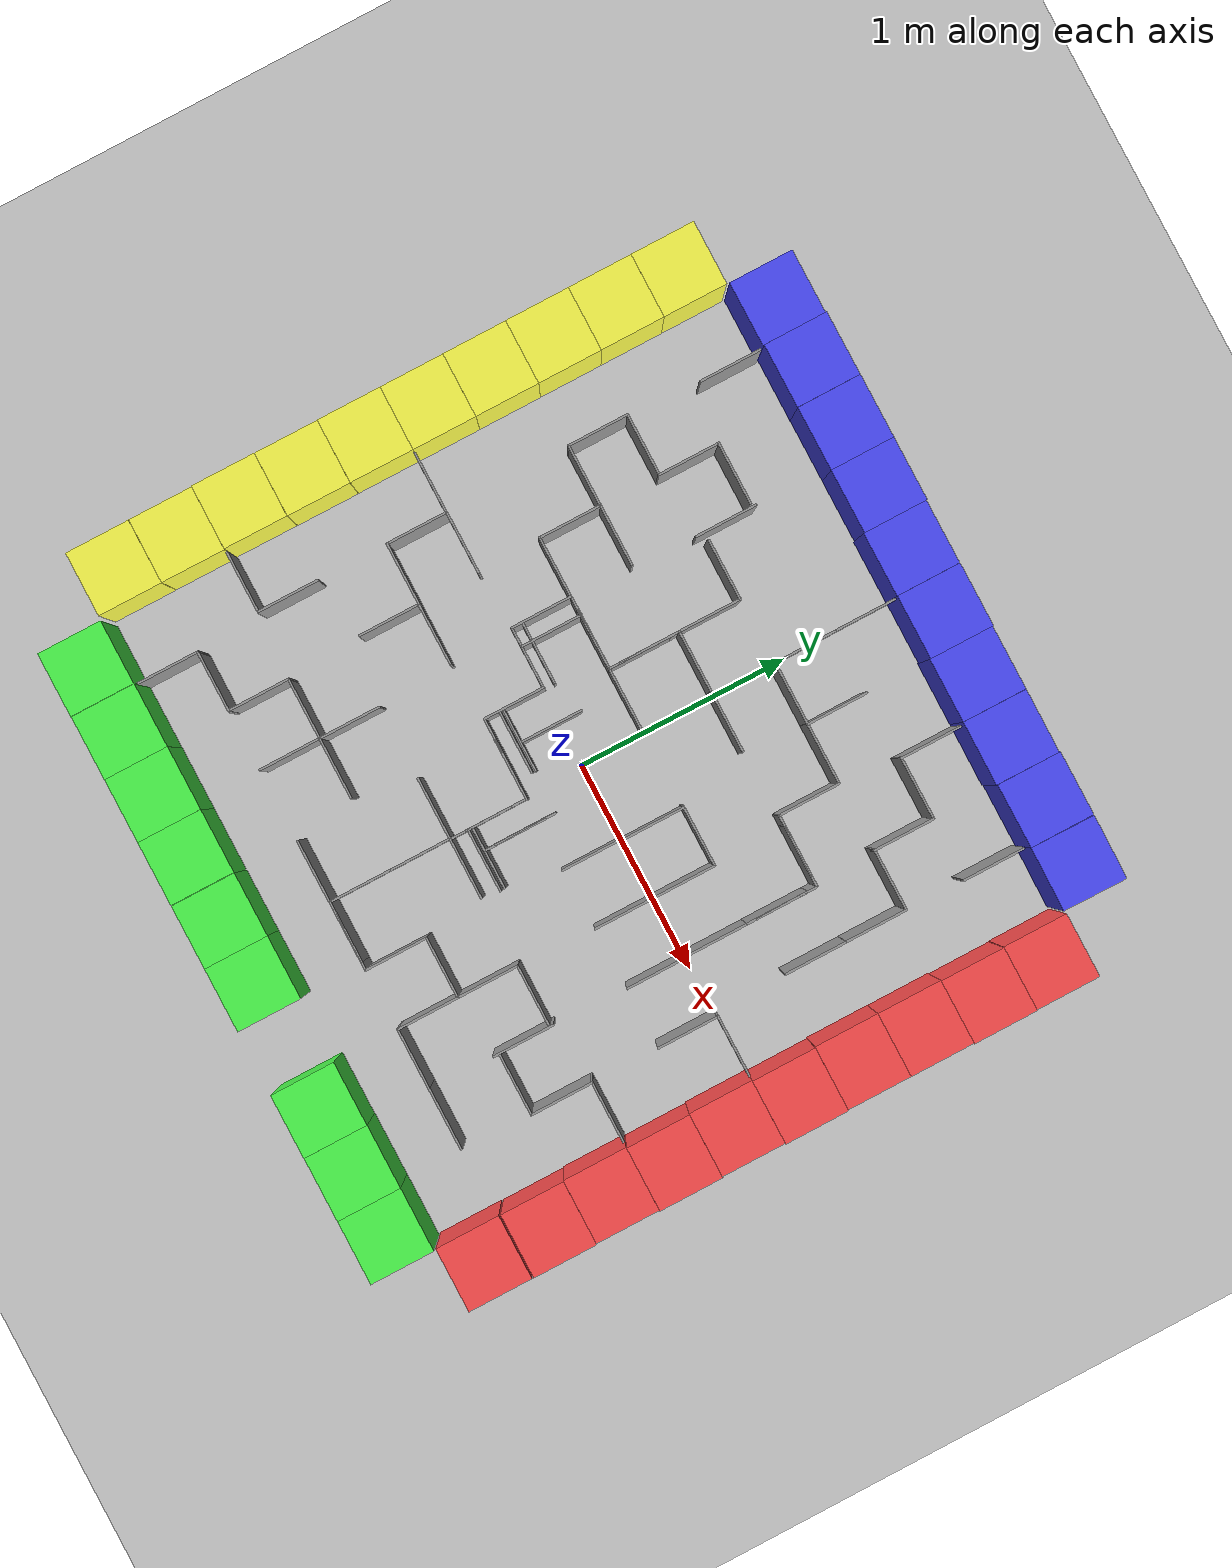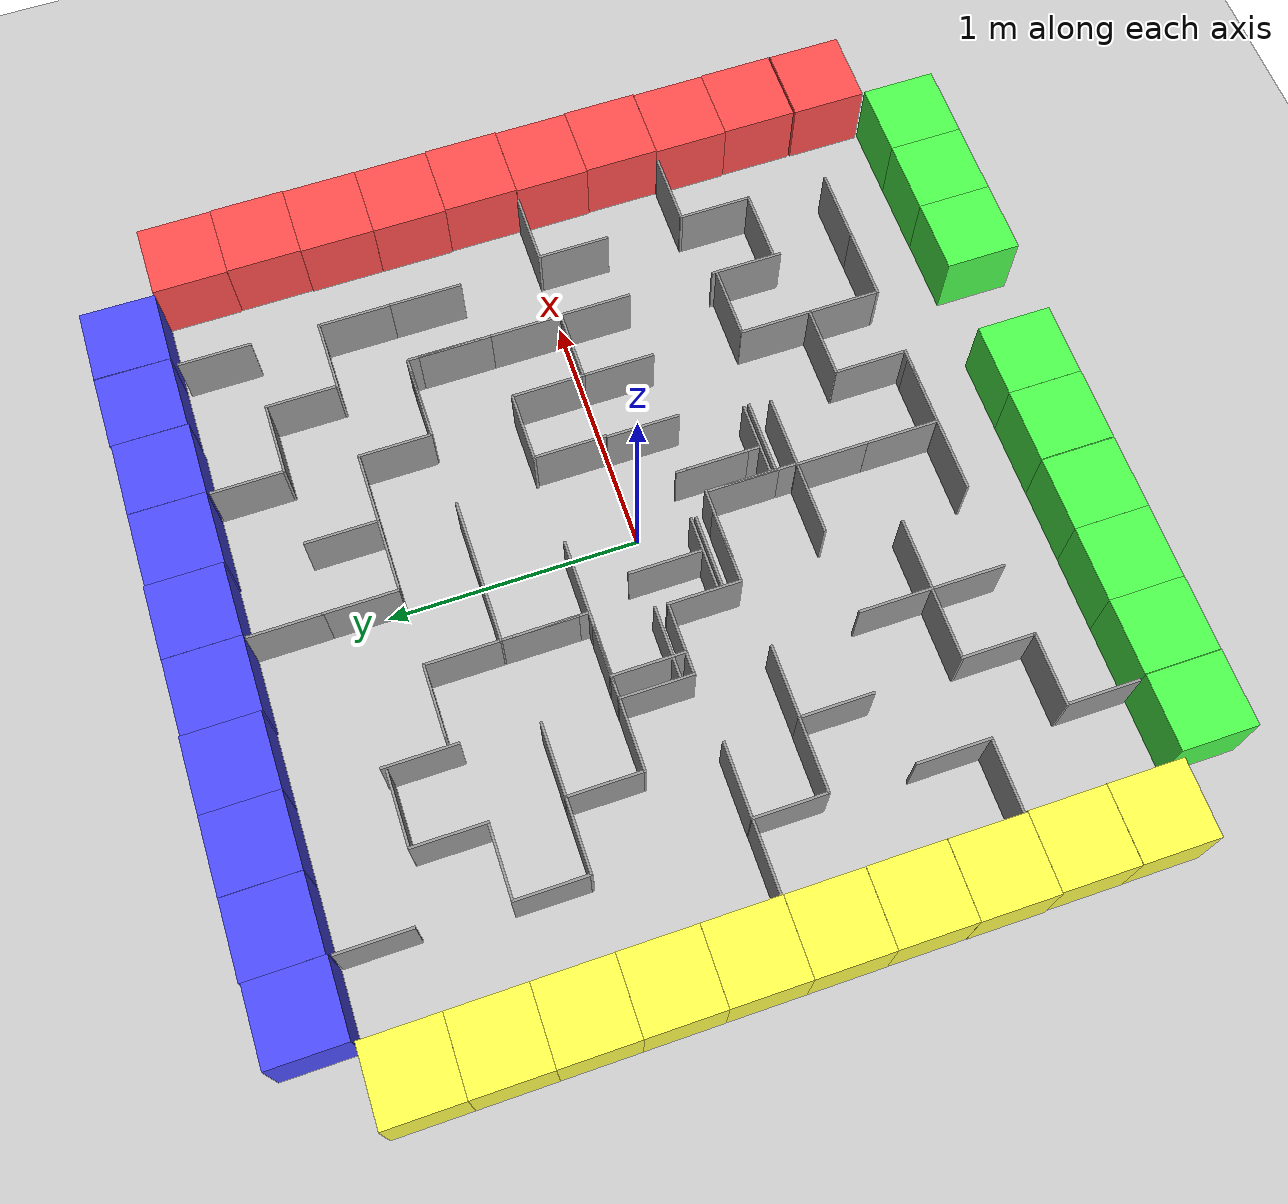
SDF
<sdf version="1.6">
 <world name="default">
  <light name="sun" type="directional">
   <pose>0 0 10 0 -0 0</pose>
   <diffuse>0.8 0.8 0.8 1</diffuse>
   <specular>0.1 0.1 0.1 1</specular>
   <attenuation>
    <range>1000</range>
    <constant>0.9</constant>
    <linear>0.01</linear>
    <quadratic>0.001</quadratic>
   </attenuation>
   <direction>-0.5 0.5 -1</direction>
  </light>
  <model name="ground_plane">
   <static>1</static>
   <link name="link">
    <collision name="collision">
     <geometry><plane><normal>0 0 1</normal><size>100 100</size></plane></geometry>
     <surface><friction><ode><mu>100</mu><mu2>50</mu2></ode></friction></surface>
    </collision>
    <visual name="visual">
     <cast_shadows>0</cast_shadows>
     <geometry><plane><normal>0 0 1</normal><size>100 100</size></plane></geometry>
     <material>
      <script><uri>file://media/materials/scripts/gazebo.material</uri><name>Gazebo/Grey</name></script>
     </material>
    </visual>
   </link>
  </model>
  <gravity>0 0 -9.8</gravity>
  <magnetic_field>6e-06 2.3e-05 -4.2e-05</magnetic_field>
  <atmosphere type="adiabatic"/>
  <physics name="default_physics" default="0" type="ode">
   <max_step_size>0.001</max_step_size>
   <real_time_factor>1</real_time_factor>
   <real_time_update_rate>1000</real_time_update_rate>
  </physics>
  <scene><ambient>0.4 0.4 0.4 1</ambient><background>0.7 0.7 0.7 1</background><shadows>1</shadows></scene>
  <spherical_coordinates>
   <surface_model>EARTH_WGS84</surface_model>
   <latitude_deg>0</latitude_deg>
   <longitude_deg>0</longitude_deg>
   <elevation>0</elevation>
   <heading_deg>0</heading_deg>
  </spherical_coordinates>
  <model name="Box_Red">
   <link name="link_0">
    <inertial>
     <mass>1</mass>
     <inertia>
      <ixx>0.166667</ixx>
      <ixy>0</ixy>
      <ixz>0</ixz>
      <iyy>0.166667</iyy>
      <iyz>0</iyz>
      <izz>0.166667</izz>
     </inertia>
    </inertial>
    <visual name="visual">
     <geometry><box><size>0.3 0.3 0.3</size></box></geometry>
     <material>
      <lighting>1</lighting>
      <script><uri>file://media/materials/scripts/gazebo.material</uri><name>Gazebo/Grey</name></script>
      <ambient>1 0.3 0.3 1</ambient>
      <diffuse>0.7 0.7 0.7 1</diffuse>
      <specular>0.01 0.01 0.01 1</specular>
      <emissive>0 0 0 1</emissive>
      <shader type="vertex"><normal_map>__default__</normal_map></shader>
     </material>
    </visual>
    <collision name="collision">
     <geometry><box><size>0.3 0.3 0.3</size></box></geometry>
     <surface>
      <friction>
       <ode><mu>1</mu><mu2>1</mu2><fdir1>0 0 0</fdir1><slip1>0</slip1><slip2>0</slip2></ode>
       <torsional>
        <coefficient>1</coefficient>
        <patch_radius>0</patch_radius>
        <surface_radius>0</surface_radius>
        <use_patch_radius>1</use_patch_radius>
        <ode><slip>0</slip></ode>
       </torsional>
      </friction>
      <bounce><restitution_coefficient>0</restitution_coefficient><threshold>1e+06</threshold></bounce>
      <contact>
       <collide_without_contact>0</collide_without_contact>
       <collide_without_contact_bitmask>1</collide_without_contact_bitmask>
       <collide_bitmask>1</collide_bitmask>
       <ode>
        <soft_cfm>0</soft_cfm>
        <soft_erp>0.2</soft_erp>
        <kp>1e+13</kp>
        <kd>1</kd>
        <max_vel>0.01</max_vel>
        <min_depth>0</min_depth>
       </ode>
       <bullet>
        <split_impulse>1</split_impulse>
        <split_impulse_penetration_threshold>-0.01</split_impulse_penetration_threshold>
        <soft_cfm>0</soft_cfm>
        <soft_erp>0.2</soft_erp>
        <kp>1e+13</kp>
        <kd>1</kd>
       </bullet>
      </contact>
     </surface>
    </collision>
   </link>
   <static>0</static>
   <pose>1.65636 1.36 0.15 0 -0 -4.7e-05</pose>
  </model>
  <model name="Box_Red_clone">
   <link name="link_0">
    <inertial>
     <mass>1</mass>
     <inertia>
      <ixx>0.166667</ixx>
      <ixy>0</ixy>
      <ixz>0</ixz>
      <iyy>0.166667</iyy>
      <iyz>0</iyz>
      <izz>0.166667</izz>
     </inertia>
    </inertial>
    <visual name="visual">
     <geometry><box><size>0.3 0.3 0.3</size></box></geometry>
     <material>
      <lighting>1</lighting>
      <script><uri>file://media/materials/scripts/gazebo.material</uri><name>Gazebo/Grey</name></script>
      <ambient>1 0.3 0.3 1</ambient>
      <diffuse>0.7 0.7 0.7 1</diffuse>
      <specular>0.01 0.01 0.01 1</specular>
      <emissive>0 0 0 1</emissive>
      <shader type="vertex"><normal_map>__default__</normal_map></shader>
     </material>
    </visual>
    <collision name="collision">
     <geometry><box><size>0.3 0.3 0.3</size></box></geometry>
     <surface>
      <friction>
       <ode><mu>1</mu><mu2>1</mu2><fdir1>0 0 0</fdir1><slip1>0</slip1><slip2>0</slip2></ode>
       <torsional>
        <coefficient>1</coefficient>
        <patch_radius>0</patch_radius>
        <surface_radius>0</surface_radius>
        <use_patch_radius>1</use_patch_radius>
        <ode><slip>0</slip></ode>
       </torsional>
      </friction>
      <bounce><restitution_coefficient>0</restitution_coefficient><threshold>1e+06</threshold></bounce>
      <contact>
       <collide_without_contact>0</collide_without_contact>
       <collide_without_contact_bitmask>1</collide_without_contact_bitmask>
       <collide_bitmask>1</collide_bitmask>
       <ode>
        <soft_cfm>0</soft_cfm>
        <soft_erp>0.2</soft_erp>
        <kp>1e+13</kp>
        <kd>1</kd>
        <max_vel>0.01</max_vel>
        <min_depth>0</min_depth>
       </ode>
       <bullet>
        <split_impulse>1</split_impulse>
        <split_impulse_penetration_threshold>-0.01</split_impulse_penetration_threshold>
        <soft_cfm>0</soft_cfm>
        <soft_erp>0.2</soft_erp>
        <kp>1e+13</kp>
        <kd>1</kd>
       </bullet>
      </contact>
     </surface>
    </collision>
   </link>
   <static>0</static>
   <pose>1.6595 1.05998 0.15 0 -0 8.8e-05</pose>
  </model>
  <model name="Box_Red_clone_0">
   <link name="link_0">
    <inertial>
     <mass>1</mass>
     <inertia>
      <ixx>0.166667</ixx>
      <ixy>0</ixy>
      <ixz>0</ixz>
      <iyy>0.166667</iyy>
      <iyz>0</iyz>
      <izz>0.166667</izz>
     </inertia>
    </inertial>
    <visual name="visual">
     <geometry><box><size>0.3 0.3 0.3</size></box></geometry>
     <material>
      <lighting>1</lighting>
      <script><uri>file://media/materials/scripts/gazebo.material</uri><name>Gazebo/Grey</name></script>
      <ambient>1 0.3 0.3 1</ambient>
      <diffuse>0.7 0.7 0.7 1</diffuse>
      <specular>0.01 0.01 0.01 1</specular>
      <emissive>0 0 0 1</emissive>
      <shader type="vertex"><normal_map>__default__</normal_map></shader>
     </material>
    </visual>
    <collision name="collision">
     <geometry><box><size>0.3 0.3 0.3</size></box></geometry>
     <surface>
      <friction>
       <ode><mu>1</mu><mu2>1</mu2><fdir1>0 0 0</fdir1><slip1>0</slip1><slip2>0</slip2></ode>
       <torsional>
        <coefficient>1</coefficient>
        <patch_radius>0</patch_radius>
        <surface_radius>0</surface_radius>
        <use_patch_radius>1</use_patch_radius>
        <ode><slip>0</slip></ode>
       </torsional>
      </friction>
      <bounce><restitution_coefficient>0</restitution_coefficient><threshold>1e+06</threshold></bounce>
      <contact>
       <collide_without_contact>0</collide_without_contact>
       <collide_without_contact_bitmask>1</collide_without_contact_bitmask>
       <collide_bitmask>1</collide_bitmask>
       <ode>
        <soft_cfm>0</soft_cfm>
        <soft_erp>0.2</soft_erp>
        <kp>1e+13</kp>
        <kd>1</kd>
        <max_vel>0.01</max_vel>
        <min_depth>0</min_depth>
       </ode>
       <bullet>
        <split_impulse>1</split_impulse>
        <split_impulse_penetration_threshold>-0.01</split_impulse_penetration_threshold>
        <soft_cfm>0</soft_cfm>
        <soft_erp>0.2</soft_erp>
        <kp>1e+13</kp>
        <kd>1</kd>
       </bullet>
      </contact>
     </surface>
    </collision>
   </link>
   <static>0</static>
   <pose>1.65601 0.759963 0.15 0 -0 5.9e-05</pose>
  </model>
  <model name="Box_Red_clone_1">
   <link name="link_0">
    <inertial>
     <mass>1</mass>
     <inertia>
      <ixx>0.166667</ixx>
      <ixy>0</ixy>
      <ixz>0</ixz>
      <iyy>0.166667</iyy>
      <iyz>0</iyz>
      <izz>0.166667</izz>
     </inertia>
    </inertial>
    <visual name="visual">
     <geometry><box><size>0.3 0.3 0.3</size></box></geometry>
     <material>
      <lighting>1</lighting>
      <script><uri>file://media/materials/scripts/gazebo.material</uri><name>Gazebo/Grey</name></script>
      <ambient>1 0.3 0.3 1</ambient>
      <diffuse>0.7 0.7 0.7 1</diffuse>
      <specular>0.01 0.01 0.01 1</specular>
      <emissive>0 0 0 1</emissive>
      <shader type="vertex"><normal_map>__default__</normal_map></shader>
     </material>
    </visual>
    <collision name="collision">
     <geometry><box><size>0.3 0.3 0.3</size></box></geometry>
     <surface>
      <friction>
       <ode><mu>1</mu><mu2>1</mu2><fdir1>0 0 0</fdir1><slip1>0</slip1><slip2>0</slip2></ode>
       <torsional>
        <coefficient>1</coefficient>
        <patch_radius>0</patch_radius>
        <surface_radius>0</surface_radius>
        <use_patch_radius>1</use_patch_radius>
        <ode><slip>0</slip></ode>
       </torsional>
      </friction>
      <bounce><restitution_coefficient>0</restitution_coefficient><threshold>1e+06</threshold></bounce>
      <contact>
       <collide_without_contact>0</collide_without_contact>
       <collide_without_contact_bitmask>1</collide_without_contact_bitmask>
       <collide_bitmask>1</collide_bitmask>
       <ode>
        <soft_cfm>0</soft_cfm>
        <soft_erp>0.2</soft_erp>
        <kp>1e+13</kp>
        <kd>1</kd>
        <max_vel>0.01</max_vel>
        <min_depth>0</min_depth>
       </ode>
       <bullet>
        <split_impulse>1</split_impulse>
        <split_impulse_penetration_threshold>-0.01</split_impulse_penetration_threshold>
        <soft_cfm>0</soft_cfm>
        <soft_erp>0.2</soft_erp>
        <kp>1e+13</kp>
        <kd>1</kd>
       </bullet>
      </contact>
     </surface>
    </collision>
   </link>
   <static>0</static>
   <pose>1.65528 0.459952 0.15 0 -0 0.0001</pose>
  </model>
  <model name="Box_Red_clone_2">
   <link name="link_0">
    <inertial>
     <mass>1</mass>
     <inertia>
      <ixx>0.166667</ixx>
      <ixy>0</ixy>
      <ixz>0</ixz>
      <iyy>0.166667</iyy>
      <iyz>0</iyz>
      <izz>0.166667</izz>
     </inertia>
    </inertial>
    <visual name="visual">
     <geometry><box><size>0.3 0.3 0.3</size></box></geometry>
     <material>
      <lighting>1</lighting>
      <script><uri>file://media/materials/scripts/gazebo.material</uri><name>Gazebo/Grey</name></script>
      <ambient>1 0.3 0.3 1</ambient>
      <diffuse>0.7 0.7 0.7 1</diffuse>
      <specular>0.01 0.01 0.01 1</specular>
      <emissive>0 0 0 1</emissive>
      <shader type="vertex"><normal_map>__default__</normal_map></shader>
     </material>
    </visual>
    <collision name="collision">
     <geometry><box><size>0.3 0.3 0.3</size></box></geometry>
     <surface>
      <friction>
       <ode><mu>1</mu><mu2>1</mu2><fdir1>0 0 0</fdir1><slip1>0</slip1><slip2>0</slip2></ode>
       <torsional>
        <coefficient>1</coefficient>
        <patch_radius>0</patch_radius>
        <surface_radius>0</surface_radius>
        <use_patch_radius>1</use_patch_radius>
        <ode><slip>0</slip></ode>
       </torsional>
      </friction>
      <bounce><restitution_coefficient>0</restitution_coefficient><threshold>1e+06</threshold></bounce>
      <contact>
       <collide_without_contact>0</collide_without_contact>
       <collide_without_contact_bitmask>1</collide_without_contact_bitmask>
       <collide_bitmask>1</collide_bitmask>
       <ode>
        <soft_cfm>0</soft_cfm>
        <soft_erp>0.2</soft_erp>
        <kp>1e+13</kp>
        <kd>1</kd>
        <max_vel>0.01</max_vel>
        <min_depth>0</min_depth>
       </ode>
       <bullet>
        <split_impulse>1</split_impulse>
        <split_impulse_penetration_threshold>-0.01</split_impulse_penetration_threshold>
        <soft_cfm>0</soft_cfm>
        <soft_erp>0.2</soft_erp>
        <kp>1e+13</kp>
        <kd>1</kd>
       </bullet>
      </contact>
     </surface>
    </collision>
   </link>
   <static>0</static>
   <pose>1.65948 0.159881 0.15 0 -0 0.000522</pose>
  </model>
  <model name="Box_Red_clone_3">
   <link name="link_0">
    <inertial>
     <mass>1</mass>
     <inertia>
      <ixx>0.166667</ixx>
      <ixy>0</ixy>
      <ixz>0</ixz>
      <iyy>0.166667</iyy>
      <iyz>0</iyz>
      <izz>0.166667</izz>
     </inertia>
    </inertial>
    <visual name="visual">
     <geometry><box><size>0.3 0.3 0.3</size></box></geometry>
     <material>
      <lighting>1</lighting>
      <script><uri>file://media/materials/scripts/gazebo.material</uri><name>Gazebo/Grey</name></script>
      <ambient>1 0.3 0.3 1</ambient>
      <diffuse>0.7 0.7 0.7 1</diffuse>
      <specular>0.01 0.01 0.01 1</specular>
      <emissive>0 0 0 1</emissive>
      <shader type="vertex"><normal_map>__default__</normal_map></shader>
     </material>
    </visual>
    <collision name="collision">
     <geometry><box><size>0.3 0.3 0.3</size></box></geometry>
     <surface>
      <friction>
       <ode><mu>1</mu><mu2>1</mu2><fdir1>0 0 0</fdir1><slip1>0</slip1><slip2>0</slip2></ode>
       <torsional>
        <coefficient>1</coefficient>
        <patch_radius>0</patch_radius>
        <surface_radius>0</surface_radius>
        <use_patch_radius>1</use_patch_radius>
        <ode><slip>0</slip></ode>
       </torsional>
      </friction>
      <bounce><restitution_coefficient>0</restitution_coefficient><threshold>1e+06</threshold></bounce>
      <contact>
       <collide_without_contact>0</collide_without_contact>
       <collide_without_contact_bitmask>1</collide_without_contact_bitmask>
       <collide_bitmask>1</collide_bitmask>
       <ode>
        <soft_cfm>0</soft_cfm>
        <soft_erp>0.2</soft_erp>
        <kp>1e+13</kp>
        <kd>1</kd>
        <max_vel>0.01</max_vel>
        <min_depth>0</min_depth>
       </ode>
       <bullet>
        <split_impulse>1</split_impulse>
        <split_impulse_penetration_threshold>-0.01</split_impulse_penetration_threshold>
        <soft_cfm>0</soft_cfm>
        <soft_erp>0.2</soft_erp>
        <kp>1e+13</kp>
        <kd>1</kd>
       </bullet>
      </contact>
     </surface>
    </collision>
   </link>
   <static>0</static>
   <pose>1.65506 -0.140171 0.15 0 -0 0.000201</pose>
  </model>
  <model name="Box_Red_clone_4">
   <link name="link_0">
    <inertial>
     <mass>1</mass>
     <inertia>
      <ixx>0.166667</ixx>
      <ixy>0</ixy>
      <ixz>0</ixz>
      <iyy>0.166667</iyy>
      <iyz>0</iyz>
      <izz>0.166667</izz>
     </inertia>
    </inertial>
    <visual name="visual">
     <geometry><box><size>0.3 0.3 0.3</size></box></geometry>
     <material>
      <lighting>1</lighting>
      <script><uri>file://media/materials/scripts/gazebo.material</uri><name>Gazebo/Grey</name></script>
      <ambient>1 0.3 0.3 1</ambient>
      <diffuse>0.7 0.7 0.7 1</diffuse>
      <specular>0.01 0.01 0.01 1</specular>
      <emissive>0 0 0 1</emissive>
      <shader type="vertex"><normal_map>__default__</normal_map></shader>
     </material>
    </visual>
    <collision name="collision">
     <geometry><box><size>0.3 0.3 0.3</size></box></geometry>
     <surface>
      <friction>
       <ode><mu>1</mu><mu2>1</mu2><fdir1>0 0 0</fdir1><slip1>0</slip1><slip2>0</slip2></ode>
       <torsional>
        <coefficient>1</coefficient>
        <patch_radius>0</patch_radius>
        <surface_radius>0</surface_radius>
        <use_patch_radius>1</use_patch_radius>
        <ode><slip>0</slip></ode>
       </torsional>
      </friction>
      <bounce><restitution_coefficient>0</restitution_coefficient><threshold>1e+06</threshold></bounce>
      <contact>
       <collide_without_contact>0</collide_without_contact>
       <collide_without_contact_bitmask>1</collide_without_contact_bitmask>
       <collide_bitmask>1</collide_bitmask>
       <ode>
        <soft_cfm>0</soft_cfm>
        <soft_erp>0.2</soft_erp>
        <kp>1e+13</kp>
        <kd>1</kd>
        <max_vel>0.01</max_vel>
        <min_depth>0</min_depth>
       </ode>
       <bullet>
        <split_impulse>1</split_impulse>
        <split_impulse_penetration_threshold>-0.01</split_impulse_penetration_threshold>
        <soft_cfm>0</soft_cfm>
        <soft_erp>0.2</soft_erp>
        <kp>1e+13</kp>
        <kd>1</kd>
       </bullet>
      </contact>
     </surface>
    </collision>
   </link>
   <static>0</static>
   <pose>1.65976 -0.440197 0.15 0 -0 0.000127</pose>
  </model>
  <model name="Box_Red_clone_5">
   <link name="link_0">
    <inertial>
     <mass>1</mass>
     <inertia>
      <ixx>0.166667</ixx>
      <ixy>0</ixy>
      <ixz>0</ixz>
      <iyy>0.166667</iyy>
      <iyz>0</iyz>
      <izz>0.166667</izz>
     </inertia>
    </inertial>
    <visual name="visual">
     <geometry><box><size>0.3 0.3 0.3</size></box></geometry>
     <material>
      <lighting>1</lighting>
      <script><uri>file://media/materials/scripts/gazebo.material</uri><name>Gazebo/Grey</name></script>
      <ambient>1 0.3 0.3 1</ambient>
      <diffuse>0.7 0.7 0.7 1</diffuse>
      <specular>0.01 0.01 0.01 1</specular>
      <emissive>0 0 0 1</emissive>
      <shader type="vertex"><normal_map>__default__</normal_map></shader>
     </material>
    </visual>
    <collision name="collision">
     <geometry><box><size>0.3 0.3 0.3</size></box></geometry>
     <surface>
      <friction>
       <ode><mu>1</mu><mu2>1</mu2><fdir1>0 0 0</fdir1><slip1>0</slip1><slip2>0</slip2></ode>
       <torsional>
        <coefficient>1</coefficient>
        <patch_radius>0</patch_radius>
        <surface_radius>0</surface_radius>
        <use_patch_radius>1</use_patch_radius>
        <ode><slip>0</slip></ode>
       </torsional>
      </friction>
      <bounce><restitution_coefficient>0</restitution_coefficient><threshold>1e+06</threshold></bounce>
      <contact>
       <collide_without_contact>0</collide_without_contact>
       <collide_without_contact_bitmask>1</collide_without_contact_bitmask>
       <collide_bitmask>1</collide_bitmask>
       <ode>
        <soft_cfm>0</soft_cfm>
        <soft_erp>0.2</soft_erp>
        <kp>1e+13</kp>
        <kd>1</kd>
        <max_vel>0.01</max_vel>
        <min_depth>0</min_depth>
       </ode>
       <bullet>
        <split_impulse>1</split_impulse>
        <split_impulse_penetration_threshold>-0.01</split_impulse_penetration_threshold>
        <soft_cfm>0</soft_cfm>
        <soft_erp>0.2</soft_erp>
        <kp>1e+13</kp>
        <kd>1</kd>
       </bullet>
      </contact>
     </surface>
    </collision>
   </link>
   <static>0</static>
   <pose>1.65527 -0.740271 0.15 0 -0 -0.000112</pose>
  </model>
  <model name="Box_Red_clone_6">
   <link name="link_0">
    <inertial>
     <mass>1</mass>
     <inertia>
      <ixx>0.166667</ixx>
      <ixy>0</ixy>
      <ixz>0</ixz>
      <iyy>0.166667</iyy>
      <iyz>0</iyz>
      <izz>0.166667</izz>
     </inertia>
    </inertial>
    <visual name="visual">
     <geometry><box><size>0.3 0.3 0.3</size></box></geometry>
     <material>
      <lighting>1</lighting>
      <script><uri>file://media/materials/scripts/gazebo.material</uri><name>Gazebo/Grey</name></script>
      <ambient>1 0.3 0.3 1</ambient>
      <diffuse>0.7 0.7 0.7 1</diffuse>
      <specular>0.01 0.01 0.01 1</specular>
      <emissive>0 0 0 1</emissive>
      <shader type="vertex"><normal_map>__default__</normal_map></shader>
     </material>
    </visual>
    <collision name="collision">
     <geometry><box><size>0.3 0.3 0.3</size></box></geometry>
     <surface>
      <friction>
       <ode><mu>1</mu><mu2>1</mu2><fdir1>0 0 0</fdir1><slip1>0</slip1><slip2>0</slip2></ode>
       <torsional>
        <coefficient>1</coefficient>
        <patch_radius>0</patch_radius>
        <surface_radius>0</surface_radius>
        <use_patch_radius>1</use_patch_radius>
        <ode><slip>0</slip></ode>
       </torsional>
      </friction>
      <bounce><restitution_coefficient>0</restitution_coefficient><threshold>1e+06</threshold></bounce>
      <contact>
       <collide_without_contact>0</collide_without_contact>
       <collide_without_contact_bitmask>1</collide_without_contact_bitmask>
       <collide_bitmask>1</collide_bitmask>
       <ode>
        <soft_cfm>0</soft_cfm>
        <soft_erp>0.2</soft_erp>
        <kp>1e+13</kp>
        <kd>1</kd>
        <max_vel>0.01</max_vel>
        <min_depth>0</min_depth>
       </ode>
       <bullet>
        <split_impulse>1</split_impulse>
        <split_impulse_penetration_threshold>-0.01</split_impulse_penetration_threshold>
        <soft_cfm>0</soft_cfm>
        <soft_erp>0.2</soft_erp>
        <kp>1e+13</kp>
        <kd>1</kd>
       </bullet>
      </contact>
     </surface>
    </collision>
   </link>
   <static>0</static>
   <pose>1.65902 -1.04031 0.15 0 -0 2.8e-05</pose>
  </model>
  <model name="Box_Red_clone_7">
   <link name="link_0">
    <inertial>
     <mass>1</mass>
     <inertia>
      <ixx>0.166667</ixx>
      <ixy>0</ixy>
      <ixz>0</ixz>
      <iyy>0.166667</iyy>
      <iyz>0</iyz>
      <izz>0.166667</izz>
     </inertia>
    </inertial>
    <visual name="visual">
     <geometry><box><size>0.3 0.3 0.3</size></box></geometry>
     <material>
      <lighting>1</lighting>
      <script><uri>file://media/materials/scripts/gazebo.material</uri><name>Gazebo/Grey</name></script>
      <ambient>1 0.3 0.3 1</ambient>
      <diffuse>0.7 0.7 0.7 1</diffuse>
      <specular>0.01 0.01 0.01 1</specular>
      <emissive>0 0 0 1</emissive>
      <shader type="vertex"><normal_map>__default__</normal_map></shader>
     </material>
    </visual>
    <collision name="collision">
     <geometry><box><size>0.3 0.3 0.3</size></box></geometry>
     <surface>
      <friction>
       <ode><mu>1</mu><mu2>1</mu2><fdir1>0 0 0</fdir1><slip1>0</slip1><slip2>0</slip2></ode>
       <torsional>
        <coefficient>1</coefficient>
        <patch_radius>0</patch_radius>
        <surface_radius>0</surface_radius>
        <use_patch_radius>1</use_patch_radius>
        <ode><slip>0</slip></ode>
       </torsional>
      </friction>
      <bounce><restitution_coefficient>0</restitution_coefficient><threshold>1e+06</threshold></bounce>
      <contact>
       <collide_without_contact>0</collide_without_contact>
       <collide_without_contact_bitmask>1</collide_without_contact_bitmask>
       <collide_bitmask>1</collide_bitmask>
       <ode>
        <soft_cfm>0</soft_cfm>
        <soft_erp>0.2</soft_erp>
        <kp>1e+13</kp>
        <kd>1</kd>
        <max_vel>0.01</max_vel>
        <min_depth>0</min_depth>
       </ode>
       <bullet>
        <split_impulse>1</split_impulse>
        <split_impulse_penetration_threshold>-0.01</split_impulse_penetration_threshold>
        <soft_cfm>0</soft_cfm>
        <soft_erp>0.2</soft_erp>
        <kp>1e+13</kp>
        <kd>1</kd>
       </bullet>
      </contact>
     </surface>
    </collision>
   </link>
   <static>0</static>
   <pose>1.65728 -1.34759 0.15 0 -0 3.8e-05</pose>
  </model>
  <model name="Box_Blue">
   <link name="link_0">
    <inertial>
     <mass>1</mass>
     <inertia>
      <ixx>0.166667</ixx>
      <ixy>0</ixy>
      <ixz>0</ixz>
      <iyy>0.166667</iyy>
      <iyz>0</iyz>
      <izz>0.166667</izz>
     </inertia>
    </inertial>
    <visual name="visual">
     <geometry><box><size>0.3 0.3 0.3</size></box></geometry>
     <material>
      <lighting>1</lighting>
      <script><uri>file://media/materials/scripts/gazebo.material</uri><name>Gazebo/Grey</name></script>
      <ambient>0.3 0.3 1 1</ambient>
      <diffuse>0.7 0.7 0.7 1</diffuse>
      <specular>0.01 0.01 0.01 1</specular>
      <emissive>0 0 0 1</emissive>
      <shader type="vertex"><normal_map>__default__</normal_map></shader>
     </material>
    </visual>
    <collision name="collision">
     <geometry><box><size>0.3 0.3 0.3</size></box></geometry>
     <surface>
      <friction>
       <ode><mu>1</mu><mu2>1</mu2><fdir1>0 0 0</fdir1><slip1>0</slip1><slip2>0</slip2></ode>
       <torsional>
        <coefficient>1</coefficient>
        <patch_radius>0</patch_radius>
        <surface_radius>0</surface_radius>
        <use_patch_radius>1</use_patch_radius>
        <ode><slip>0</slip></ode>
       </torsional>
      </friction>
      <bounce><restitution_coefficient>0</restitution_coefficient><threshold>1e+06</threshold></bounce>
      <contact>
       <collide_without_contact>0</collide_without_contact>
       <collide_without_contact_bitmask>1</collide_without_contact_bitmask>
       <collide_bitmask>1</collide_bitmask>
       <ode>
        <soft_cfm>0</soft_cfm>
        <soft_erp>0.2</soft_erp>
        <kp>1e+13</kp>
        <kd>1</kd>
        <max_vel>0.01</max_vel>
        <min_depth>0</min_depth>
       </ode>
       <bullet>
        <split_impulse>1</split_impulse>
        <split_impulse_penetration_threshold>-0.01</split_impulse_penetration_threshold>
        <soft_cfm>0</soft_cfm>
        <soft_erp>0.2</soft_erp>
        <kp>1e+13</kp>
        <kd>1</kd>
       </bullet>
      </contact>
     </surface>
    </collision>
   </link>
   <static>0</static>
   <pose>1.34428 1.65663 0.15 0 -0 -0.010737</pose>
  </model>
  <model name="Box_Green">
   <link name="link_0">
    <inertial>
     <mass>1</mass>
     <inertia>
      <ixx>0.166667</ixx>
      <ixy>0</ixy>
      <ixz>0</ixz>
      <iyy>0.166667</iyy>
      <iyz>0</iyz>
      <izz>0.166667</izz>
     </inertia>
    </inertial>
    <visual name="visual">
     <geometry><box><size>0.3 0.3 0.3</size></box></geometry>
     <material>
      <lighting>1</lighting>
      <script><uri>file://media/materials/scripts/gazebo.material</uri><name>Gazebo/Grey</name></script>
      <ambient>0.3 1 0.3 1</ambient>
      <diffuse>0.7 0.7 0.7 1</diffuse>
      <specular>0.01 0.01 0.01 1</specular>
      <emissive>0 0 0 1</emissive>
      <shader type="vertex"><normal_map>__default__</normal_map></shader>
     </material>
    </visual>
    <collision name="collision">
     <geometry><box><size>0.3 0.3 0.3</size></box></geometry>
     <surface>
      <friction>
       <ode><mu>1</mu><mu2>1</mu2><fdir1>0 0 0</fdir1><slip1>0</slip1><slip2>0</slip2></ode>
       <torsional>
        <coefficient>1</coefficient>
        <patch_radius>0</patch_radius>
        <surface_radius>0</surface_radius>
        <use_patch_radius>1</use_patch_radius>
        <ode><slip>0</slip></ode>
       </torsional>
      </friction>
      <bounce><restitution_coefficient>0</restitution_coefficient><threshold>1e+06</threshold></bounce>
      <contact>
       <collide_without_contact>0</collide_without_contact>
       <collide_without_contact_bitmask>1</collide_without_contact_bitmask>
       <collide_bitmask>1</collide_bitmask>
       <ode>
        <soft_cfm>0</soft_cfm>
        <soft_erp>0.2</soft_erp>
        <kp>1e+13</kp>
        <kd>1</kd>
        <max_vel>0.01</max_vel>
        <min_depth>0</min_depth>
       </ode>
       <bullet>
        <split_impulse>1</split_impulse>
        <split_impulse_penetration_threshold>-0.01</split_impulse_penetration_threshold>
        <soft_cfm>0</soft_cfm>
        <soft_erp>0.2</soft_erp>
        <kp>1e+13</kp>
        <kd>1</kd>
       </bullet>
      </contact>
     </surface>
    </collision>
   </link>
   <static>0</static>
   <pose>1.36264 -1.65861 0.15 0 -0 -0.000198</pose>
  </model>
  <model name="Box_Yellow">
   <link name="link_0">
    <inertial>
     <mass>1</mass>
     <inertia>
      <ixx>0.166667</ixx>
      <ixy>0</ixy>
      <ixz>0</ixz>
      <iyy>0.166667</iyy>
      <iyz>0</iyz>
      <izz>0.166667</izz>
     </inertia>
    </inertial>
    <visual name="visual">
     <geometry><box><size>0.3 0.3 0.3</size></box></geometry>
     <material>
      <lighting>1</lighting>
      <script><uri>file://media/materials/scripts/gazebo.material</uri><name>Gazebo/Grey</name></script>
      <ambient>1 1 0.3 1</ambient>
      <diffuse>0.7 0.7 0.7 1</diffuse>
      <specular>0.01 0.01 0.01 1</specular>
      <emissive>0 0 0 1</emissive>
      <shader type="vertex"><normal_map>__default__</normal_map></shader>
     </material>
    </visual>
    <collision name="collision">
     <geometry><box><size>0.3 0.3 0.3</size></box></geometry>
     <surface>
      <friction>
       <ode><mu>1</mu><mu2>1</mu2><fdir1>0 0 0</fdir1><slip1>0</slip1><slip2>0</slip2></ode>
       <torsional>
        <coefficient>1</coefficient>
        <patch_radius>0</patch_radius>
        <surface_radius>0</surface_radius>
        <use_patch_radius>1</use_patch_radius>
        <ode><slip>0</slip></ode>
       </torsional>
      </friction>
      <bounce><restitution_coefficient>0</restitution_coefficient><threshold>1e+06</threshold></bounce>
      <contact>
       <collide_without_contact>0</collide_without_contact>
       <collide_without_contact_bitmask>1</collide_without_contact_bitmask>
       <collide_bitmask>1</collide_bitmask>
       <ode>
        <soft_cfm>0</soft_cfm>
        <soft_erp>0.2</soft_erp>
        <kp>1e+13</kp>
        <kd>1</kd>
        <max_vel>0.01</max_vel>
        <min_depth>0</min_depth>
       </ode>
       <bullet>
        <split_impulse>1</split_impulse>
        <split_impulse_penetration_threshold>-0.01</split_impulse_penetration_threshold>
        <soft_cfm>0</soft_cfm>
        <soft_erp>0.2</soft_erp>
        <kp>1e+13</kp>
        <kd>1</kd>
       </bullet>
      </contact>
     </surface>
    </collision>
   </link>
   <static>0</static>
   <pose>-1.66342 -1.35735 0.15 0 -0 -0.001735</pose>
  </model>
  <model name="Box_Green_clone">
   <link name="link_0">
    <inertial>
     <mass>1</mass>
     <inertia>
      <ixx>0.166667</ixx>
      <ixy>0</ixy>
      <ixz>0</ixz>
      <iyy>0.166667</iyy>
      <iyz>0</iyz>
      <izz>0.166667</izz>
     </inertia>
    </inertial>
    <visual name="visual">
     <geometry><box><size>0.3 0.3 0.3</size></box></geometry>
     <material>
      <lighting>1</lighting>
      <script><uri>file://media/materials/scripts/gazebo.material</uri><name>Gazebo/Grey</name></script>
      <ambient>0.3 1 0.3 1</ambient>
      <diffuse>0.7 0.7 0.7 1</diffuse>
      <specular>0.01 0.01 0.01 1</specular>
      <emissive>0 0 0 1</emissive>
      <shader type="vertex"><normal_map>__default__</normal_map></shader>
     </material>
    </visual>
    <collision name="collision">
     <geometry><box><size>0.3 0.3 0.3</size></box></geometry>
     <surface>
      <friction>
       <ode><mu>1</mu><mu2>1</mu2><fdir1>0 0 0</fdir1><slip1>0</slip1><slip2>0</slip2></ode>
       <torsional>
        <coefficient>1</coefficient>
        <patch_radius>0</patch_radius>
        <surface_radius>0</surface_radius>
        <use_patch_radius>1</use_patch_radius>
        <ode><slip>0</slip></ode>
       </torsional>
      </friction>
      <bounce><restitution_coefficient>0</restitution_coefficient><threshold>1e+06</threshold></bounce>
      <contact>
       <collide_without_contact>0</collide_without_contact>
       <collide_without_contact_bitmask>1</collide_without_contact_bitmask>
       <collide_bitmask>1</collide_bitmask>
       <ode>
        <soft_cfm>0</soft_cfm>
        <soft_erp>0.2</soft_erp>
        <kp>1e+13</kp>
        <kd>1</kd>
        <max_vel>0.01</max_vel>
        <min_depth>0</min_depth>
       </ode>
       <bullet>
        <split_impulse>1</split_impulse>
        <split_impulse_penetration_threshold>-0.01</split_impulse_penetration_threshold>
        <soft_cfm>0</soft_cfm>
        <soft_erp>0.2</soft_erp>
        <kp>1e+13</kp>
        <kd>1</kd>
       </bullet>
      </contact>
     </surface>
    </collision>
   </link>
   <static>0</static>
   <pose>1.06264 -1.65908 0.15 -0 -0 -0.000192</pose>
  </model>
  <model name="Box_Green_clone_0">
   <link name="link_0">
    <inertial>
     <mass>1</mass>
     <inertia>
      <ixx>0.166667</ixx>
      <ixy>0</ixy>
      <ixz>0</ixz>
      <iyy>0.166667</iyy>
      <iyz>0</iyz>
      <izz>0.166667</izz>
     </inertia>
    </inertial>
    <visual name="visual">
     <geometry><box><size>0.3 0.3 0.3</size></box></geometry>
     <material>
      <lighting>1</lighting>
      <script><uri>file://media/materials/scripts/gazebo.material</uri><name>Gazebo/Grey</name></script>
      <ambient>0.3 1 0.3 1</ambient>
      <diffuse>0.7 0.7 0.7 1</diffuse>
      <specular>0.01 0.01 0.01 1</specular>
      <emissive>0 0 0 1</emissive>
      <shader type="vertex"><normal_map>__default__</normal_map></shader>
     </material>
    </visual>
    <collision name="collision">
     <geometry><box><size>0.3 0.3 0.3</size></box></geometry>
     <surface>
      <friction>
       <ode><mu>1</mu><mu2>1</mu2><fdir1>0 0 0</fdir1><slip1>0</slip1><slip2>0</slip2></ode>
       <torsional>
        <coefficient>1</coefficient>
        <patch_radius>0</patch_radius>
        <surface_radius>0</surface_radius>
        <use_patch_radius>1</use_patch_radius>
        <ode><slip>0</slip></ode>
       </torsional>
      </friction>
      <bounce><restitution_coefficient>0</restitution_coefficient><threshold>1e+06</threshold></bounce>
      <contact>
       <collide_without_contact>0</collide_without_contact>
       <collide_without_contact_bitmask>1</collide_without_contact_bitmask>
       <collide_bitmask>1</collide_bitmask>
       <ode>
        <soft_cfm>0</soft_cfm>
        <soft_erp>0.2</soft_erp>
        <kp>1e+13</kp>
        <kd>1</kd>
        <max_vel>0.01</max_vel>
        <min_depth>0</min_depth>
       </ode>
       <bullet>
        <split_impulse>1</split_impulse>
        <split_impulse_penetration_threshold>-0.01</split_impulse_penetration_threshold>
        <soft_cfm>0</soft_cfm>
        <soft_erp>0.2</soft_erp>
        <kp>1e+13</kp>
        <kd>1</kd>
       </bullet>
      </contact>
     </surface>
    </collision>
   </link>
   <static>0</static>
   <pose>0.762626 -1.6603 0.15 0 -0 -0.00019</pose>
  </model>
  <model name="Box_Green_clone_2">
   <link name="link_0">
    <inertial>
     <mass>1</mass>
     <inertia>
      <ixx>0.166667</ixx>
      <ixy>0</ixy>
      <ixz>0</ixz>
      <iyy>0.166667</iyy>
      <iyz>0</iyz>
      <izz>0.166667</izz>
     </inertia>
    </inertial>
    <visual name="visual">
     <geometry><box><size>0.3 0.3 0.3</size></box></geometry>
     <material>
      <lighting>1</lighting>
      <script><uri>file://media/materials/scripts/gazebo.material</uri><name>Gazebo/Grey</name></script>
      <ambient>0.3 1 0.3 1</ambient>
      <diffuse>0.7 0.7 0.7 1</diffuse>
      <specular>0.01 0.01 0.01 1</specular>
      <emissive>0 0 0 1</emissive>
      <shader type="vertex"><normal_map>__default__</normal_map></shader>
     </material>
    </visual>
    <collision name="collision">
     <geometry><box><size>0.3 0.3 0.3</size></box></geometry>
     <surface>
      <friction>
       <ode><mu>1</mu><mu2>1</mu2><fdir1>0 0 0</fdir1><slip1>0</slip1><slip2>0</slip2></ode>
       <torsional>
        <coefficient>1</coefficient>
        <patch_radius>0</patch_radius>
        <surface_radius>0</surface_radius>
        <use_patch_radius>1</use_patch_radius>
        <ode><slip>0</slip></ode>
       </torsional>
      </friction>
      <bounce><restitution_coefficient>0</restitution_coefficient><threshold>1e+06</threshold></bounce>
      <contact>
       <collide_without_contact>0</collide_without_contact>
       <collide_without_contact_bitmask>1</collide_without_contact_bitmask>
       <collide_bitmask>1</collide_bitmask>
       <ode>
        <soft_cfm>0</soft_cfm>
        <soft_erp>0.2</soft_erp>
        <kp>1e+13</kp>
        <kd>1</kd>
        <max_vel>0.01</max_vel>
        <min_depth>0</min_depth>
       </ode>
       <bullet>
        <split_impulse>1</split_impulse>
        <split_impulse_penetration_threshold>-0.01</split_impulse_penetration_threshold>
        <soft_cfm>0</soft_cfm>
        <soft_erp>0.2</soft_erp>
        <kp>1e+13</kp>
        <kd>1</kd>
       </bullet>
      </contact>
     </surface>
    </collision>
   </link>
   <static>0</static>
   <pose>0.162354 -1.65755 0.15 0 -0 -0.000187</pose>
  </model>
  <model name="Box_Green_clone_4">
   <link name="link_0">
    <inertial>
     <mass>1</mass>
     <inertia>
      <ixx>0.166667</ixx>
      <ixy>0</ixy>
      <ixz>0</ixz>
      <iyy>0.166667</iyy>
      <iyz>0</iyz>
      <izz>0.166667</izz>
     </inertia>
    </inertial>
    <visual name="visual">
     <geometry><box><size>0.3 0.3 0.3</size></box></geometry>
     <material>
      <lighting>1</lighting>
      <script><uri>file://media/materials/scripts/gazebo.material</uri><name>Gazebo/Grey</name></script>
      <ambient>0.3 1 0.3 1</ambient>
      <diffuse>0.7 0.7 0.7 1</diffuse>
      <specular>0.01 0.01 0.01 1</specular>
      <emissive>0 0 0 1</emissive>
      <shader type="vertex"><normal_map>__default__</normal_map></shader>
     </material>
    </visual>
    <collision name="collision">
     <geometry><box><size>0.3 0.3 0.3</size></box></geometry>
     <surface>
      <friction>
       <ode><mu>1</mu><mu2>1</mu2><fdir1>0 0 0</fdir1><slip1>0</slip1><slip2>0</slip2></ode>
       <torsional>
        <coefficient>1</coefficient>
        <patch_radius>0</patch_radius>
        <surface_radius>0</surface_radius>
        <use_patch_radius>1</use_patch_radius>
        <ode><slip>0</slip></ode>
       </torsional>
      </friction>
      <bounce><restitution_coefficient>0</restitution_coefficient><threshold>1e+06</threshold></bounce>
      <contact>
       <collide_without_contact>0</collide_without_contact>
       <collide_without_contact_bitmask>1</collide_without_contact_bitmask>
       <collide_bitmask>1</collide_bitmask>
       <ode>
        <soft_cfm>0</soft_cfm>
        <soft_erp>0.2</soft_erp>
        <kp>1e+13</kp>
        <kd>1</kd>
        <max_vel>0.01</max_vel>
        <min_depth>0</min_depth>
       </ode>
       <bullet>
        <split_impulse>1</split_impulse>
        <split_impulse_penetration_threshold>-0.01</split_impulse_penetration_threshold>
        <soft_cfm>0</soft_cfm>
        <soft_erp>0.2</soft_erp>
        <kp>1e+13</kp>
        <kd>1</kd>
       </bullet>
      </contact>
     </surface>
    </collision>
   </link>
   <static>0</static>
   <pose>-0.440485 -1.65793 0.15 0 -0 -6.7e-05</pose>
  </model>
  <model name="Box_Green_clone_5">
   <link name="link_0">
    <inertial>
     <mass>1</mass>
     <inertia>
      <ixx>0.166667</ixx>
      <ixy>0</ixy>
      <ixz>0</ixz>
      <iyy>0.166667</iyy>
      <iyz>0</iyz>
      <izz>0.166667</izz>
     </inertia>
    </inertial>
    <visual name="visual">
     <geometry><box><size>0.3 0.3 0.3</size></box></geometry>
     <material>
      <lighting>1</lighting>
      <script><uri>file://media/materials/scripts/gazebo.material</uri><name>Gazebo/Grey</name></script>
      <ambient>0.3 1 0.3 1</ambient>
      <diffuse>0.7 0.7 0.7 1</diffuse>
      <specular>0.01 0.01 0.01 1</specular>
      <emissive>0 0 0 1</emissive>
      <shader type="vertex"><normal_map>__default__</normal_map></shader>
     </material>
    </visual>
    <collision name="collision">
     <geometry><box><size>0.3 0.3 0.3</size></box></geometry>
     <surface>
      <friction>
       <ode><mu>1</mu><mu2>1</mu2><fdir1>0 0 0</fdir1><slip1>0</slip1><slip2>0</slip2></ode>
       <torsional>
        <coefficient>1</coefficient>
        <patch_radius>0</patch_radius>
        <surface_radius>0</surface_radius>
        <use_patch_radius>1</use_patch_radius>
        <ode><slip>0</slip></ode>
       </torsional>
      </friction>
      <bounce><restitution_coefficient>0</restitution_coefficient><threshold>1e+06</threshold></bounce>
      <contact>
       <collide_without_contact>0</collide_without_contact>
       <collide_without_contact_bitmask>1</collide_without_contact_bitmask>
       <collide_bitmask>1</collide_bitmask>
       <ode>
        <soft_cfm>0</soft_cfm>
        <soft_erp>0.2</soft_erp>
        <kp>1e+13</kp>
        <kd>1</kd>
        <max_vel>0.01</max_vel>
        <min_depth>0</min_depth>
       </ode>
       <bullet>
        <split_impulse>1</split_impulse>
        <split_impulse_penetration_threshold>-0.01</split_impulse_penetration_threshold>
        <soft_cfm>0</soft_cfm>
        <soft_erp>0.2</soft_erp>
        <kp>1e+13</kp>
        <kd>1</kd>
       </bullet>
      </contact>
     </surface>
    </collision>
   </link>
   <static>0</static>
   <pose>-0.740618 -1.65773 0.15 0 -0 0.000345</pose>
  </model>
  <model name="Box_Green_clone_6">
   <link name="link_0">
    <inertial>
     <mass>1</mass>
     <inertia>
      <ixx>0.166667</ixx>
      <ixy>0</ixy>
      <ixz>0</ixz>
      <iyy>0.166667</iyy>
      <iyz>0</iyz>
      <izz>0.166667</izz>
     </inertia>
    </inertial>
    <visual name="visual">
     <geometry><box><size>0.3 0.3 0.3</size></box></geometry>
     <material>
      <lighting>1</lighting>
      <script><uri>file://media/materials/scripts/gazebo.material</uri><name>Gazebo/Grey</name></script>
      <ambient>0.3 1 0.3 1</ambient>
      <diffuse>0.7 0.7 0.7 1</diffuse>
      <specular>0.01 0.01 0.01 1</specular>
      <emissive>0 0 0 1</emissive>
      <shader type="vertex"><normal_map>__default__</normal_map></shader>
     </material>
    </visual>
    <collision name="collision">
     <geometry><box><size>0.3 0.3 0.3</size></box></geometry>
     <surface>
      <friction>
       <ode><mu>1</mu><mu2>1</mu2><fdir1>0 0 0</fdir1><slip1>0</slip1><slip2>0</slip2></ode>
       <torsional>
        <coefficient>1</coefficient>
        <patch_radius>0</patch_radius>
        <surface_radius>0</surface_radius>
        <use_patch_radius>1</use_patch_radius>
        <ode><slip>0</slip></ode>
       </torsional>
      </friction>
      <bounce><restitution_coefficient>0</restitution_coefficient><threshold>1e+06</threshold></bounce>
      <contact>
       <collide_without_contact>0</collide_without_contact>
       <collide_without_contact_bitmask>1</collide_without_contact_bitmask>
       <collide_bitmask>1</collide_bitmask>
       <ode>
        <soft_cfm>0</soft_cfm>
        <soft_erp>0.2</soft_erp>
        <kp>1e+13</kp>
        <kd>1</kd>
        <max_vel>0.01</max_vel>
        <min_depth>0</min_depth>
       </ode>
       <bullet>
        <split_impulse>1</split_impulse>
        <split_impulse_penetration_threshold>-0.01</split_impulse_penetration_threshold>
        <soft_cfm>0</soft_cfm>
        <soft_erp>0.2</soft_erp>
        <kp>1e+13</kp>
        <kd>1</kd>
       </bullet>
      </contact>
     </surface>
    </collision>
   </link>
   <static>0</static>
   <pose>-1.04062 -1.65808 0.15 0 -0 0.000344</pose>
  </model>
  <model name="Box_Yellow_clone">
   <link name="link_0">
    <inertial>
     <mass>1</mass>
     <inertia>
      <ixx>0.166667</ixx>
      <ixy>0</ixy>
      <ixz>0</ixz>
      <iyy>0.166667</iyy>
      <iyz>0</iyz>
      <izz>0.166667</izz>
     </inertia>
    </inertial>
    <visual name="visual">
     <geometry><box><size>0.3 0.3 0.3</size></box></geometry>
     <material>
      <lighting>1</lighting>
      <script><uri>file://media/materials/scripts/gazebo.material</uri><name>Gazebo/Grey</name></script>
      <ambient>1 1 0.3 1</ambient>
      <diffuse>0.7 0.7 0.7 1</diffuse>
      <specular>0.01 0.01 0.01 1</specular>
      <emissive>0 0 0 1</emissive>
      <shader type="vertex"><normal_map>__default__</normal_map></shader>
     </material>
    </visual>
    <collision name="collision">
     <geometry><box><size>0.3 0.3 0.3</size></box></geometry>
     <surface>
      <friction>
       <ode><mu>1</mu><mu2>1</mu2><fdir1>0 0 0</fdir1><slip1>0</slip1><slip2>0</slip2></ode>
       <torsional>
        <coefficient>1</coefficient>
        <patch_radius>0</patch_radius>
        <surface_radius>0</surface_radius>
        <use_patch_radius>1</use_patch_radius>
        <ode><slip>0</slip></ode>
       </torsional>
      </friction>
      <bounce><restitution_coefficient>0</restitution_coefficient><threshold>1e+06</threshold></bounce>
      <contact>
       <collide_without_contact>0</collide_without_contact>
       <collide_without_contact_bitmask>1</collide_without_contact_bitmask>
       <collide_bitmask>1</collide_bitmask>
       <ode>
        <soft_cfm>0</soft_cfm>
        <soft_erp>0.2</soft_erp>
        <kp>1e+13</kp>
        <kd>1</kd>
        <max_vel>0.01</max_vel>
        <min_depth>0</min_depth>
       </ode>
       <bullet>
        <split_impulse>1</split_impulse>
        <split_impulse_penetration_threshold>-0.01</split_impulse_penetration_threshold>
        <soft_cfm>0</soft_cfm>
        <soft_erp>0.2</soft_erp>
        <kp>1e+13</kp>
        <kd>1</kd>
       </bullet>
      </contact>
     </surface>
    </collision>
   </link>
   <static>0</static>
   <pose>-1.66313 -1.05692 0.15 0 0 -0.004486</pose>
  </model>
  <model name="Box_Yellow_clone_0">
   <link name="link_0">
    <inertial>
     <mass>1</mass>
     <inertia>
      <ixx>0.166667</ixx>
      <ixy>0</ixy>
      <ixz>0</ixz>
      <iyy>0.166667</iyy>
      <iyz>0</iyz>
      <izz>0.166667</izz>
     </inertia>
    </inertial>
    <visual name="visual">
     <geometry><box><size>0.3 0.3 0.3</size></box></geometry>
     <material>
      <lighting>1</lighting>
      <script><uri>file://media/materials/scripts/gazebo.material</uri><name>Gazebo/Grey</name></script>
      <ambient>1 1 0.3 1</ambient>
      <diffuse>0.7 0.7 0.7 1</diffuse>
      <specular>0.01 0.01 0.01 1</specular>
      <emissive>0 0 0 1</emissive>
      <shader type="vertex"><normal_map>__default__</normal_map></shader>
     </material>
    </visual>
    <collision name="collision">
     <geometry><box><size>0.3 0.3 0.3</size></box></geometry>
     <surface>
      <friction>
       <ode><mu>1</mu><mu2>1</mu2><fdir1>0 0 0</fdir1><slip1>0</slip1><slip2>0</slip2></ode>
       <torsional>
        <coefficient>1</coefficient>
        <patch_radius>0</patch_radius>
        <surface_radius>0</surface_radius>
        <use_patch_radius>1</use_patch_radius>
        <ode><slip>0</slip></ode>
       </torsional>
      </friction>
      <bounce><restitution_coefficient>0</restitution_coefficient><threshold>1e+06</threshold></bounce>
      <contact>
       <collide_without_contact>0</collide_without_contact>
       <collide_without_contact_bitmask>1</collide_without_contact_bitmask>
       <collide_bitmask>1</collide_bitmask>
       <ode>
        <soft_cfm>0</soft_cfm>
        <soft_erp>0.2</soft_erp>
        <kp>1e+13</kp>
        <kd>1</kd>
        <max_vel>0.01</max_vel>
        <min_depth>0</min_depth>
       </ode>
       <bullet>
        <split_impulse>1</split_impulse>
        <split_impulse_penetration_threshold>-0.01</split_impulse_penetration_threshold>
        <soft_cfm>0</soft_cfm>
        <soft_erp>0.2</soft_erp>
        <kp>1e+13</kp>
        <kd>1</kd>
       </bullet>
      </contact>
     </surface>
    </collision>
   </link>
   <static>0</static>
   <pose>-1.66556 -0.756814 0.15 -0 -0 -0.005116</pose>
  </model>
  <model name="Box_Yellow_clone_1">
   <link name="link_0">
    <inertial>
     <mass>1</mass>
     <inertia>
      <ixx>0.166667</ixx>
      <ixy>0</ixy>
      <ixz>0</ixz>
      <iyy>0.166667</iyy>
      <iyz>0</iyz>
      <izz>0.166667</izz>
     </inertia>
    </inertial>
    <visual name="visual">
     <geometry><box><size>0.3 0.3 0.3</size></box></geometry>
     <material>
      <lighting>1</lighting>
      <script><uri>file://media/materials/scripts/gazebo.material</uri><name>Gazebo/Grey</name></script>
      <ambient>1 1 0.3 1</ambient>
      <diffuse>0.7 0.7 0.7 1</diffuse>
      <specular>0.01 0.01 0.01 1</specular>
      <emissive>0 0 0 1</emissive>
      <shader type="vertex"><normal_map>__default__</normal_map></shader>
     </material>
    </visual>
    <collision name="collision">
     <geometry><box><size>0.3 0.3 0.3</size></box></geometry>
     <surface>
      <friction>
       <ode><mu>1</mu><mu2>1</mu2><fdir1>0 0 0</fdir1><slip1>0</slip1><slip2>0</slip2></ode>
       <torsional>
        <coefficient>1</coefficient>
        <patch_radius>0</patch_radius>
        <surface_radius>0</surface_radius>
        <use_patch_radius>1</use_patch_radius>
        <ode><slip>0</slip></ode>
       </torsional>
      </friction>
      <bounce><restitution_coefficient>0</restitution_coefficient><threshold>1e+06</threshold></bounce>
      <contact>
       <collide_without_contact>0</collide_without_contact>
       <collide_without_contact_bitmask>1</collide_without_contact_bitmask>
       <collide_bitmask>1</collide_bitmask>
       <ode>
        <soft_cfm>0</soft_cfm>
        <soft_erp>0.2</soft_erp>
        <kp>1e+13</kp>
        <kd>1</kd>
        <max_vel>0.01</max_vel>
        <min_depth>0</min_depth>
       </ode>
       <bullet>
        <split_impulse>1</split_impulse>
        <split_impulse_penetration_threshold>-0.01</split_impulse_penetration_threshold>
        <soft_cfm>0</soft_cfm>
        <soft_erp>0.2</soft_erp>
        <kp>1e+13</kp>
        <kd>1</kd>
       </bullet>
      </contact>
     </surface>
    </collision>
   </link>
   <static>0</static>
   <pose>-1.66358 -0.456605 0.15 0 -0 -0.003685</pose>
  </model>
  <model name="Box_Yellow_clone_2">
   <link name="link_0">
    <inertial>
     <mass>1</mass>
     <inertia>
      <ixx>0.166667</ixx>
      <ixy>0</ixy>
      <ixz>0</ixz>
      <iyy>0.166667</iyy>
      <iyz>0</iyz>
      <izz>0.166667</izz>
     </inertia>
    </inertial>
    <visual name="visual">
     <geometry><box><size>0.3 0.3 0.3</size></box></geometry>
     <material>
      <lighting>1</lighting>
      <script><uri>file://media/materials/scripts/gazebo.material</uri><name>Gazebo/Grey</name></script>
      <ambient>1 1 0.3 1</ambient>
      <diffuse>0.7 0.7 0.7 1</diffuse>
      <specular>0.01 0.01 0.01 1</specular>
      <emissive>0 0 0 1</emissive>
      <shader type="vertex"><normal_map>__default__</normal_map></shader>
     </material>
    </visual>
    <collision name="collision">
     <geometry><box><size>0.3 0.3 0.3</size></box></geometry>
     <surface>
      <friction>
       <ode><mu>1</mu><mu2>1</mu2><fdir1>0 0 0</fdir1><slip1>0</slip1><slip2>0</slip2></ode>
       <torsional>
        <coefficient>1</coefficient>
        <patch_radius>0</patch_radius>
        <surface_radius>0</surface_radius>
        <use_patch_radius>1</use_patch_radius>
        <ode><slip>0</slip></ode>
       </torsional>
      </friction>
      <bounce><restitution_coefficient>0</restitution_coefficient><threshold>1e+06</threshold></bounce>
      <contact>
       <collide_without_contact>0</collide_without_contact>
       <collide_without_contact_bitmask>1</collide_without_contact_bitmask>
       <collide_bitmask>1</collide_bitmask>
       <ode>
        <soft_cfm>0</soft_cfm>
        <soft_erp>0.2</soft_erp>
        <kp>1e+13</kp>
        <kd>1</kd>
        <max_vel>0.01</max_vel>
        <min_depth>0</min_depth>
       </ode>
       <bullet>
        <split_impulse>1</split_impulse>
        <split_impulse_penetration_threshold>-0.01</split_impulse_penetration_threshold>
        <soft_cfm>0</soft_cfm>
        <soft_erp>0.2</soft_erp>
        <kp>1e+13</kp>
        <kd>1</kd>
       </bullet>
      </contact>
     </surface>
    </collision>
   </link>
   <static>0</static>
   <pose>-1.66351 -0.156388 0.15 -0 -0 -0.002256</pose>
  </model>
  <model name="Box_Yellow_clone_3">
   <link name="link_0">
    <inertial>
     <mass>1</mass>
     <inertia>
      <ixx>0.166667</ixx>
      <ixy>0</ixy>
      <ixz>0</ixz>
      <iyy>0.166667</iyy>
      <iyz>0</iyz>
      <izz>0.166667</izz>
     </inertia>
    </inertial>
    <visual name="visual">
     <geometry><box><size>0.3 0.3 0.3</size></box></geometry>
     <material>
      <lighting>1</lighting>
      <script><uri>file://media/materials/scripts/gazebo.material</uri><name>Gazebo/Grey</name></script>
      <ambient>1 1 0.3 1</ambient>
      <diffuse>0.7 0.7 0.7 1</diffuse>
      <specular>0.01 0.01 0.01 1</specular>
      <emissive>0 0 0 1</emissive>
      <shader type="vertex"><normal_map>__default__</normal_map></shader>
     </material>
    </visual>
    <collision name="collision">
     <geometry><box><size>0.3 0.3 0.3</size></box></geometry>
     <surface>
      <friction>
       <ode><mu>1</mu><mu2>1</mu2><fdir1>0 0 0</fdir1><slip1>0</slip1><slip2>0</slip2></ode>
       <torsional>
        <coefficient>1</coefficient>
        <patch_radius>0</patch_radius>
        <surface_radius>0</surface_radius>
        <use_patch_radius>1</use_patch_radius>
        <ode><slip>0</slip></ode>
       </torsional>
      </friction>
      <bounce><restitution_coefficient>0</restitution_coefficient><threshold>1e+06</threshold></bounce>
      <contact>
       <collide_without_contact>0</collide_without_contact>
       <collide_without_contact_bitmask>1</collide_without_contact_bitmask>
       <collide_bitmask>1</collide_bitmask>
       <ode>
        <soft_cfm>0</soft_cfm>
        <soft_erp>0.2</soft_erp>
        <kp>1e+13</kp>
        <kd>1</kd>
        <max_vel>0.01</max_vel>
        <min_depth>0</min_depth>
       </ode>
       <bullet>
        <split_impulse>1</split_impulse>
        <split_impulse_penetration_threshold>-0.01</split_impulse_penetration_threshold>
        <soft_cfm>0</soft_cfm>
        <soft_erp>0.2</soft_erp>
        <kp>1e+13</kp>
        <kd>1</kd>
       </bullet>
      </contact>
     </surface>
    </collision>
   </link>
   <static>0</static>
   <pose>-1.66285 0.143677 0.15 0 -0 -0.001826</pose>
  </model>
  <model name="Box_Yellow_clone_4">
   <link name="link_0">
    <inertial>
     <mass>1</mass>
     <inertia>
      <ixx>0.166667</ixx>
      <ixy>0</ixy>
      <ixz>0</ixz>
      <iyy>0.166667</iyy>
      <iyz>0</iyz>
      <izz>0.166667</izz>
     </inertia>
    </inertial>
    <visual name="visual">
     <geometry><box><size>0.3 0.3 0.3</size></box></geometry>
     <material>
      <lighting>1</lighting>
      <script><uri>file://media/materials/scripts/gazebo.material</uri><name>Gazebo/Grey</name></script>
      <ambient>1 1 0.3 1</ambient>
      <diffuse>0.7 0.7 0.7 1</diffuse>
      <specular>0.01 0.01 0.01 1</specular>
      <emissive>0 0 0 1</emissive>
      <shader type="vertex"><normal_map>__default__</normal_map></shader>
     </material>
    </visual>
    <collision name="collision">
     <geometry><box><size>0.3 0.3 0.3</size></box></geometry>
     <surface>
      <friction>
       <ode><mu>1</mu><mu2>1</mu2><fdir1>0 0 0</fdir1><slip1>0</slip1><slip2>0</slip2></ode>
       <torsional>
        <coefficient>1</coefficient>
        <patch_radius>0</patch_radius>
        <surface_radius>0</surface_radius>
        <use_patch_radius>1</use_patch_radius>
        <ode><slip>0</slip></ode>
       </torsional>
      </friction>
      <bounce><restitution_coefficient>0</restitution_coefficient><threshold>1e+06</threshold></bounce>
      <contact>
       <collide_without_contact>0</collide_without_contact>
       <collide_without_contact_bitmask>1</collide_without_contact_bitmask>
       <collide_bitmask>1</collide_bitmask>
       <ode>
        <soft_cfm>0</soft_cfm>
        <soft_erp>0.2</soft_erp>
        <kp>1e+13</kp>
        <kd>1</kd>
        <max_vel>0.01</max_vel>
        <min_depth>0</min_depth>
       </ode>
       <bullet>
        <split_impulse>1</split_impulse>
        <split_impulse_penetration_threshold>-0.01</split_impulse_penetration_threshold>
        <soft_cfm>0</soft_cfm>
        <soft_erp>0.2</soft_erp>
        <kp>1e+13</kp>
        <kd>1</kd>
       </bullet>
      </contact>
     </surface>
    </collision>
   </link>
   <static>0</static>
   <pose>-1.66277 0.443739 0.149998 -5e-06 7e-06 -0.001463</pose>
  </model>
  <model name="Box_Yellow_clone_5">
   <link name="link_0">
    <inertial>
     <mass>1</mass>
     <inertia>
      <ixx>0.166667</ixx>
      <ixy>0</ixy>
      <ixz>0</ixz>
      <iyy>0.166667</iyy>
      <iyz>0</iyz>
      <izz>0.166667</izz>
     </inertia>
    </inertial>
    <visual name="visual">
     <geometry><box><size>0.3 0.3 0.3</size></box></geometry>
     <material>
      <lighting>1</lighting>
      <script><uri>file://media/materials/scripts/gazebo.material</uri><name>Gazebo/Grey</name></script>
      <ambient>1 1 0.3 1</ambient>
      <diffuse>0.7 0.7 0.7 1</diffuse>
      <specular>0.01 0.01 0.01 1</specular>
      <emissive>0 0 0 1</emissive>
      <shader type="vertex"><normal_map>__default__</normal_map></shader>
     </material>
    </visual>
    <collision name="collision">
     <geometry><box><size>0.3 0.3 0.3</size></box></geometry>
     <surface>
      <friction>
       <ode><mu>1</mu><mu2>1</mu2><fdir1>0 0 0</fdir1><slip1>0</slip1><slip2>0</slip2></ode>
       <torsional>
        <coefficient>1</coefficient>
        <patch_radius>0</patch_radius>
        <surface_radius>0</surface_radius>
        <use_patch_radius>1</use_patch_radius>
        <ode><slip>0</slip></ode>
       </torsional>
      </friction>
      <bounce><restitution_coefficient>0</restitution_coefficient><threshold>1e+06</threshold></bounce>
      <contact>
       <collide_without_contact>0</collide_without_contact>
       <collide_without_contact_bitmask>1</collide_without_contact_bitmask>
       <collide_bitmask>1</collide_bitmask>
       <ode>
        <soft_cfm>0</soft_cfm>
        <soft_erp>0.2</soft_erp>
        <kp>1e+13</kp>
        <kd>1</kd>
        <max_vel>0.01</max_vel>
        <min_depth>0</min_depth>
       </ode>
       <bullet>
        <split_impulse>1</split_impulse>
        <split_impulse_penetration_threshold>-0.01</split_impulse_penetration_threshold>
        <soft_cfm>0</soft_cfm>
        <soft_erp>0.2</soft_erp>
        <kp>1e+13</kp>
        <kd>1</kd>
       </bullet>
      </contact>
     </surface>
    </collision>
   </link>
   <static>0</static>
   <pose>-1.66285 0.743811 0.15 0 -0 -0.001002</pose>
  </model>
  <model name="Box_Yellow_clone_6">
   <link name="link_0">
    <inertial>
     <mass>1</mass>
     <inertia>
      <ixx>0.166667</ixx>
      <ixy>0</ixy>
      <ixz>0</ixz>
      <iyy>0.166667</iyy>
      <iyz>0</iyz>
      <izz>0.166667</izz>
     </inertia>
    </inertial>
    <visual name="visual">
     <geometry><box><size>0.3 0.3 0.3</size></box></geometry>
     <material>
      <lighting>1</lighting>
      <script><uri>file://media/materials/scripts/gazebo.material</uri><name>Gazebo/Grey</name></script>
      <ambient>1 1 0.3 1</ambient>
      <diffuse>0.7 0.7 0.7 1</diffuse>
      <specular>0.01 0.01 0.01 1</specular>
      <emissive>0 0 0 1</emissive>
      <shader type="vertex"><normal_map>__default__</normal_map></shader>
     </material>
    </visual>
    <collision name="collision">
     <geometry><box><size>0.3 0.3 0.3</size></box></geometry>
     <surface>
      <friction>
       <ode><mu>1</mu><mu2>1</mu2><fdir1>0 0 0</fdir1><slip1>0</slip1><slip2>0</slip2></ode>
       <torsional>
        <coefficient>1</coefficient>
        <patch_radius>0</patch_radius>
        <surface_radius>0</surface_radius>
        <use_patch_radius>1</use_patch_radius>
        <ode><slip>0</slip></ode>
       </torsional>
      </friction>
      <bounce><restitution_coefficient>0</restitution_coefficient><threshold>1e+06</threshold></bounce>
      <contact>
       <collide_without_contact>0</collide_without_contact>
       <collide_without_contact_bitmask>1</collide_without_contact_bitmask>
       <collide_bitmask>1</collide_bitmask>
       <ode>
        <soft_cfm>0</soft_cfm>
        <soft_erp>0.2</soft_erp>
        <kp>1e+13</kp>
        <kd>1</kd>
        <max_vel>0.01</max_vel>
        <min_depth>0</min_depth>
       </ode>
       <bullet>
        <split_impulse>1</split_impulse>
        <split_impulse_penetration_threshold>-0.01</split_impulse_penetration_threshold>
        <soft_cfm>0</soft_cfm>
        <soft_erp>0.2</soft_erp>
        <kp>1e+13</kp>
        <kd>1</kd>
       </bullet>
      </contact>
     </surface>
    </collision>
   </link>
   <static>0</static>
   <pose>-1.66287 1.04381 0.15 -0 -0 -0.001002</pose>
  </model>
  <model name="Box_Yellow_clone_7">
   <link name="link_0">
    <inertial>
     <mass>1</mass>
     <inertia>
      <ixx>0.166667</ixx>
      <ixy>0</ixy>
      <ixz>0</ixz>
      <iyy>0.166667</iyy>
      <iyz>0</iyz>
      <izz>0.166667</izz>
     </inertia>
    </inertial>
    <visual name="visual">
     <geometry><box><size>0.3 0.3 0.3</size></box></geometry>
     <material>
      <lighting>1</lighting>
      <script><uri>file://media/materials/scripts/gazebo.material</uri><name>Gazebo/Grey</name></script>
      <ambient>1 1 0.3 1</ambient>
      <diffuse>0.7 0.7 0.7 1</diffuse>
      <specular>0.01 0.01 0.01 1</specular>
      <emissive>0 0 0 1</emissive>
      <shader type="vertex"><normal_map>__default__</normal_map></shader>
     </material>
    </visual>
    <collision name="collision">
     <geometry><box><size>0.3 0.3 0.3</size></box></geometry>
     <surface>
      <friction>
       <ode><mu>1</mu><mu2>1</mu2><fdir1>0 0 0</fdir1><slip1>0</slip1><slip2>0</slip2></ode>
       <torsional>
        <coefficient>1</coefficient>
        <patch_radius>0</patch_radius>
        <surface_radius>0</surface_radius>
        <use_patch_radius>1</use_patch_radius>
        <ode><slip>0</slip></ode>
       </torsional>
      </friction>
      <bounce><restitution_coefficient>0</restitution_coefficient><threshold>1e+06</threshold></bounce>
      <contact>
       <collide_without_contact>0</collide_without_contact>
       <collide_without_contact_bitmask>1</collide_without_contact_bitmask>
       <collide_bitmask>1</collide_bitmask>
       <ode>
        <soft_cfm>0</soft_cfm>
        <soft_erp>0.2</soft_erp>
        <kp>1e+13</kp>
        <kd>1</kd>
        <max_vel>0.01</max_vel>
        <min_depth>0</min_depth>
       </ode>
       <bullet>
        <split_impulse>1</split_impulse>
        <split_impulse_penetration_threshold>-0.01</split_impulse_penetration_threshold>
        <soft_cfm>0</soft_cfm>
        <soft_erp>0.2</soft_erp>
        <kp>1e+13</kp>
        <kd>1</kd>
       </bullet>
      </contact>
     </surface>
    </collision>
   </link>
   <static>0</static>
   <pose>-1.66267 1.34384 0.15 -0 -0 -0.000887</pose>
  </model>
  <model name="Box_Blue_clone">
   <link name="link_0">
    <inertial>
     <mass>1</mass>
     <inertia>
      <ixx>0.166667</ixx>
      <ixy>0</ixy>
      <ixz>0</ixz>
      <iyy>0.166667</iyy>
      <iyz>0</iyz>
      <izz>0.166667</izz>
     </inertia>
    </inertial>
    <visual name="visual">
     <geometry><box><size>0.3 0.3 0.3</size></box></geometry>
     <material>
      <lighting>1</lighting>
      <script><uri>file://media/materials/scripts/gazebo.material</uri><name>Gazebo/Grey</name></script>
      <ambient>0.3 0.3 1 1</ambient>
      <diffuse>0.7 0.7 0.7 1</diffuse>
      <specular>0.01 0.01 0.01 1</specular>
      <emissive>0 0 0 1</emissive>
      <shader type="vertex"><normal_map>__default__</normal_map></shader>
     </material>
    </visual>
    <collision name="collision">
     <geometry><box><size>0.3 0.3 0.3</size></box></geometry>
     <surface>
      <friction>
       <ode><mu>1</mu><mu2>1</mu2><fdir1>0 0 0</fdir1><slip1>0</slip1><slip2>0</slip2></ode>
       <torsional>
        <coefficient>1</coefficient>
        <patch_radius>0</patch_radius>
        <surface_radius>0</surface_radius>
        <use_patch_radius>1</use_patch_radius>
        <ode><slip>0</slip></ode>
       </torsional>
      </friction>
      <bounce><restitution_coefficient>0</restitution_coefficient><threshold>1e+06</threshold></bounce>
      <contact>
       <collide_without_contact>0</collide_without_contact>
       <collide_without_contact_bitmask>1</collide_without_contact_bitmask>
       <collide_bitmask>1</collide_bitmask>
       <ode>
        <soft_cfm>0</soft_cfm>
        <soft_erp>0.2</soft_erp>
        <kp>1e+13</kp>
        <kd>1</kd>
        <max_vel>0.01</max_vel>
        <min_depth>0</min_depth>
       </ode>
       <bullet>
        <split_impulse>1</split_impulse>
        <split_impulse_penetration_threshold>-0.01</split_impulse_penetration_threshold>
        <soft_cfm>0</soft_cfm>
        <soft_erp>0.2</soft_erp>
        <kp>1e+13</kp>
        <kd>1</kd>
       </bullet>
      </contact>
     </surface>
    </collision>
   </link>
   <static>0</static>
   <pose>1.04234 1.65844 0.15 0 -0 0.000693</pose>
  </model>
  <model name="Box_Blue_clone_0">
   <link name="link_0">
    <inertial>
     <mass>1</mass>
     <inertia>
      <ixx>0.166667</ixx>
      <ixy>0</ixy>
      <ixz>0</ixz>
      <iyy>0.166667</iyy>
      <iyz>0</iyz>
      <izz>0.166667</izz>
     </inertia>
    </inertial>
    <visual name="visual">
     <geometry><box><size>0.3 0.3 0.3</size></box></geometry>
     <material>
      <lighting>1</lighting>
      <script><uri>file://media/materials/scripts/gazebo.material</uri><name>Gazebo/Grey</name></script>
      <ambient>0.3 0.3 1 1</ambient>
      <diffuse>0.7 0.7 0.7 1</diffuse>
      <specular>0.01 0.01 0.01 1</specular>
      <emissive>0 0 0 1</emissive>
      <shader type="vertex"><normal_map>__default__</normal_map></shader>
     </material>
    </visual>
    <collision name="collision">
     <geometry><box><size>0.3 0.3 0.3</size></box></geometry>
     <surface>
      <friction>
       <ode><mu>1</mu><mu2>1</mu2><fdir1>0 0 0</fdir1><slip1>0</slip1><slip2>0</slip2></ode>
       <torsional>
        <coefficient>1</coefficient>
        <patch_radius>0</patch_radius>
        <surface_radius>0</surface_radius>
        <use_patch_radius>1</use_patch_radius>
        <ode><slip>0</slip></ode>
       </torsional>
      </friction>
      <bounce><restitution_coefficient>0</restitution_coefficient><threshold>1e+06</threshold></bounce>
      <contact>
       <collide_without_contact>0</collide_without_contact>
       <collide_without_contact_bitmask>1</collide_without_contact_bitmask>
       <collide_bitmask>1</collide_bitmask>
       <ode>
        <soft_cfm>0</soft_cfm>
        <soft_erp>0.2</soft_erp>
        <kp>1e+13</kp>
        <kd>1</kd>
        <max_vel>0.01</max_vel>
        <min_depth>0</min_depth>
       </ode>
       <bullet>
        <split_impulse>1</split_impulse>
        <split_impulse_penetration_threshold>-0.01</split_impulse_penetration_threshold>
        <soft_cfm>0</soft_cfm>
        <soft_erp>0.2</soft_erp>
        <kp>1e+13</kp>
        <kd>1</kd>
       </bullet>
      </contact>
     </surface>
    </collision>
   </link>
   <static>0</static>
   <pose>0.741491 1.6543 0.15 0 -0 -0.004985</pose>
  </model>
  <model name="Box_Blue_clone_1">
   <link name="link_0">
    <inertial>
     <mass>1</mass>
     <inertia>
      <ixx>0.166667</ixx>
      <ixy>0</ixy>
      <ixz>0</ixz>
      <iyy>0.166667</iyy>
      <iyz>0</iyz>
      <izz>0.166667</izz>
     </inertia>
    </inertial>
    <visual name="visual">
     <geometry><box><size>0.3 0.3 0.3</size></box></geometry>
     <material>
      <lighting>1</lighting>
      <script><uri>file://media/materials/scripts/gazebo.material</uri><name>Gazebo/Grey</name></script>
      <ambient>0.3 0.3 1 1</ambient>
      <diffuse>0.7 0.7 0.7 1</diffuse>
      <specular>0.01 0.01 0.01 1</specular>
      <emissive>0 0 0 1</emissive>
      <shader type="vertex"><normal_map>__default__</normal_map></shader>
     </material>
    </visual>
    <collision name="collision">
     <geometry><box><size>0.3 0.3 0.3</size></box></geometry>
     <surface>
      <friction>
       <ode><mu>1</mu><mu2>1</mu2><fdir1>0 0 0</fdir1><slip1>0</slip1><slip2>0</slip2></ode>
       <torsional>
        <coefficient>1</coefficient>
        <patch_radius>0</patch_radius>
        <surface_radius>0</surface_radius>
        <use_patch_radius>1</use_patch_radius>
        <ode><slip>0</slip></ode>
       </torsional>
      </friction>
      <bounce><restitution_coefficient>0</restitution_coefficient><threshold>1e+06</threshold></bounce>
      <contact>
       <collide_without_contact>0</collide_without_contact>
       <collide_without_contact_bitmask>1</collide_without_contact_bitmask>
       <collide_bitmask>1</collide_bitmask>
       <ode>
        <soft_cfm>0</soft_cfm>
        <soft_erp>0.2</soft_erp>
        <kp>1e+13</kp>
        <kd>1</kd>
        <max_vel>0.01</max_vel>
        <min_depth>0</min_depth>
       </ode>
       <bullet>
        <split_impulse>1</split_impulse>
        <split_impulse_penetration_threshold>-0.01</split_impulse_penetration_threshold>
        <soft_cfm>0</soft_cfm>
        <soft_erp>0.2</soft_erp>
        <kp>1e+13</kp>
        <kd>1</kd>
       </bullet>
      </contact>
     </surface>
    </collision>
   </link>
   <static>0</static>
   <pose>0.440771 1.6551 0.15 0 -0 -0.000185</pose>
  </model>
  <model name="Box_Blue_clone_2">
   <link name="link_0">
    <inertial>
     <mass>1</mass>
     <inertia>
      <ixx>0.166667</ixx>
      <ixy>0</ixy>
      <ixz>0</ixz>
      <iyy>0.166667</iyy>
      <iyz>0</iyz>
      <izz>0.166667</izz>
     </inertia>
    </inertial>
    <visual name="visual">
     <geometry><box><size>0.3 0.3 0.3</size></box></geometry>
     <material>
      <lighting>1</lighting>
      <script><uri>file://media/materials/scripts/gazebo.material</uri><name>Gazebo/Grey</name></script>
      <ambient>0.3 0.3 1 1</ambient>
      <diffuse>0.7 0.7 0.7 1</diffuse>
      <specular>0.01 0.01 0.01 1</specular>
      <emissive>0 0 0 1</emissive>
      <shader type="vertex"><normal_map>__default__</normal_map></shader>
     </material>
    </visual>
    <collision name="collision">
     <geometry><box><size>0.3 0.3 0.3</size></box></geometry>
     <surface>
      <friction>
       <ode><mu>1</mu><mu2>1</mu2><fdir1>0 0 0</fdir1><slip1>0</slip1><slip2>0</slip2></ode>
       <torsional>
        <coefficient>1</coefficient>
        <patch_radius>0</patch_radius>
        <surface_radius>0</surface_radius>
        <use_patch_radius>1</use_patch_radius>
        <ode><slip>0</slip></ode>
       </torsional>
      </friction>
      <bounce><restitution_coefficient>0</restitution_coefficient><threshold>1e+06</threshold></bounce>
      <contact>
       <collide_without_contact>0</collide_without_contact>
       <collide_without_contact_bitmask>1</collide_without_contact_bitmask>
       <collide_bitmask>1</collide_bitmask>
       <ode>
        <soft_cfm>0</soft_cfm>
        <soft_erp>0.2</soft_erp>
        <kp>1e+13</kp>
        <kd>1</kd>
        <max_vel>0.01</max_vel>
        <min_depth>0</min_depth>
       </ode>
       <bullet>
        <split_impulse>1</split_impulse>
        <split_impulse_penetration_threshold>-0.01</split_impulse_penetration_threshold>
        <soft_cfm>0</soft_cfm>
        <soft_erp>0.2</soft_erp>
        <kp>1e+13</kp>
        <kd>1</kd>
       </bullet>
      </contact>
     </surface>
    </collision>
   </link>
   <static>0</static>
   <pose>0.140708 1.65944 0.15 -0 -0 -0.000601</pose>
  </model>
  <model name="Box_Blue_clone_3">
   <link name="link_0">
    <inertial>
     <mass>1</mass>
     <inertia>
      <ixx>0.166667</ixx>
      <ixy>0</ixy>
      <ixz>0</ixz>
      <iyy>0.166667</iyy>
      <iyz>0</iyz>
      <izz>0.166667</izz>
     </inertia>
    </inertial>
    <visual name="visual">
     <geometry><box><size>0.3 0.3 0.3</size></box></geometry>
     <material>
      <lighting>1</lighting>
      <script><uri>file://media/materials/scripts/gazebo.material</uri><name>Gazebo/Grey</name></script>
      <ambient>0.3 0.3 1 1</ambient>
      <diffuse>0.7 0.7 0.7 1</diffuse>
      <specular>0.01 0.01 0.01 1</specular>
      <emissive>0 0 0 1</emissive>
      <shader type="vertex"><normal_map>__default__</normal_map></shader>
     </material>
    </visual>
    <collision name="collision">
     <geometry><box><size>0.3 0.3 0.3</size></box></geometry>
     <surface>
      <friction>
       <ode><mu>1</mu><mu2>1</mu2><fdir1>0 0 0</fdir1><slip1>0</slip1><slip2>0</slip2></ode>
       <torsional>
        <coefficient>1</coefficient>
        <patch_radius>0</patch_radius>
        <surface_radius>0</surface_radius>
        <use_patch_radius>1</use_patch_radius>
        <ode><slip>0</slip></ode>
       </torsional>
      </friction>
      <bounce><restitution_coefficient>0</restitution_coefficient><threshold>1e+06</threshold></bounce>
      <contact>
       <collide_without_contact>0</collide_without_contact>
       <collide_without_contact_bitmask>1</collide_without_contact_bitmask>
       <collide_bitmask>1</collide_bitmask>
       <ode>
        <soft_cfm>0</soft_cfm>
        <soft_erp>0.2</soft_erp>
        <kp>1e+13</kp>
        <kd>1</kd>
        <max_vel>0.01</max_vel>
        <min_depth>0</min_depth>
       </ode>
       <bullet>
        <split_impulse>1</split_impulse>
        <split_impulse_penetration_threshold>-0.01</split_impulse_penetration_threshold>
        <soft_cfm>0</soft_cfm>
        <soft_erp>0.2</soft_erp>
        <kp>1e+13</kp>
        <kd>1</kd>
       </bullet>
      </contact>
     </surface>
    </collision>
   </link>
   <static>0</static>
   <pose>-0.15976 1.65815 0.15 0 -0 0.001741</pose>
  </model>
  <model name="Box_Blue_clone_4">
   <link name="link_0">
    <inertial>
     <mass>1</mass>
     <inertia>
      <ixx>0.166667</ixx>
      <ixy>0</ixy>
      <ixz>0</ixz>
      <iyy>0.166667</iyy>
      <iyz>0</iyz>
      <izz>0.166667</izz>
     </inertia>
    </inertial>
    <visual name="visual">
     <geometry><box><size>0.3 0.3 0.3</size></box></geometry>
     <material>
      <lighting>1</lighting>
      <script><uri>file://media/materials/scripts/gazebo.material</uri><name>Gazebo/Grey</name></script>
      <ambient>0.3 0.3 1 1</ambient>
      <diffuse>0.7 0.7 0.7 1</diffuse>
      <specular>0.01 0.01 0.01 1</specular>
      <emissive>0 0 0 1</emissive>
      <shader type="vertex"><normal_map>__default__</normal_map></shader>
     </material>
    </visual>
    <collision name="collision">
     <geometry><box><size>0.3 0.3 0.3</size></box></geometry>
     <surface>
      <friction>
       <ode><mu>1</mu><mu2>1</mu2><fdir1>0 0 0</fdir1><slip1>0</slip1><slip2>0</slip2></ode>
       <torsional>
        <coefficient>1</coefficient>
        <patch_radius>0</patch_radius>
        <surface_radius>0</surface_radius>
        <use_patch_radius>1</use_patch_radius>
        <ode><slip>0</slip></ode>
       </torsional>
      </friction>
      <bounce><restitution_coefficient>0</restitution_coefficient><threshold>1e+06</threshold></bounce>
      <contact>
       <collide_without_contact>0</collide_without_contact>
       <collide_without_contact_bitmask>1</collide_without_contact_bitmask>
       <collide_bitmask>1</collide_bitmask>
       <ode>
        <soft_cfm>0</soft_cfm>
        <soft_erp>0.2</soft_erp>
        <kp>1e+13</kp>
        <kd>1</kd>
        <max_vel>0.01</max_vel>
        <min_depth>0</min_depth>
       </ode>
       <bullet>
        <split_impulse>1</split_impulse>
        <split_impulse_penetration_threshold>-0.01</split_impulse_penetration_threshold>
        <soft_cfm>0</soft_cfm>
        <soft_erp>0.2</soft_erp>
        <kp>1e+13</kp>
        <kd>1</kd>
       </bullet>
      </contact>
     </surface>
    </collision>
   </link>
   <static>0</static>
   <pose>-0.45982 1.66243 0.15 0 -0 0.001525</pose>
  </model>
  <model name="Box_Blue_clone_5">
   <link name="link_0">
    <inertial>
     <mass>1</mass>
     <inertia>
      <ixx>0.166667</ixx>
      <ixy>0</ixy>
      <ixz>0</ixz>
      <iyy>0.166667</iyy>
      <iyz>0</iyz>
      <izz>0.166667</izz>
     </inertia>
    </inertial>
    <visual name="visual">
     <geometry><box><size>0.3 0.3 0.3</size></box></geometry>
     <material>
      <lighting>1</lighting>
      <script><uri>file://media/materials/scripts/gazebo.material</uri><name>Gazebo/Grey</name></script>
      <ambient>0.3 0.3 1 1</ambient>
      <diffuse>0.7 0.7 0.7 1</diffuse>
      <specular>0.01 0.01 0.01 1</specular>
      <emissive>0 0 0 1</emissive>
      <shader type="vertex"><normal_map>__default__</normal_map></shader>
     </material>
    </visual>
    <collision name="collision">
     <geometry><box><size>0.3 0.3 0.3</size></box></geometry>
     <surface>
      <friction>
       <ode><mu>1</mu><mu2>1</mu2><fdir1>0 0 0</fdir1><slip1>0</slip1><slip2>0</slip2></ode>
       <torsional>
        <coefficient>1</coefficient>
        <patch_radius>0</patch_radius>
        <surface_radius>0</surface_radius>
        <use_patch_radius>1</use_patch_radius>
        <ode><slip>0</slip></ode>
       </torsional>
      </friction>
      <bounce><restitution_coefficient>0</restitution_coefficient><threshold>1e+06</threshold></bounce>
      <contact>
       <collide_without_contact>0</collide_without_contact>
       <collide_without_contact_bitmask>1</collide_without_contact_bitmask>
       <collide_bitmask>1</collide_bitmask>
       <ode>
        <soft_cfm>0</soft_cfm>
        <soft_erp>0.2</soft_erp>
        <kp>1e+13</kp>
        <kd>1</kd>
        <max_vel>0.01</max_vel>
        <min_depth>0</min_depth>
       </ode>
       <bullet>
        <split_impulse>1</split_impulse>
        <split_impulse_penetration_threshold>-0.01</split_impulse_penetration_threshold>
        <soft_cfm>0</soft_cfm>
        <soft_erp>0.2</soft_erp>
        <kp>1e+13</kp>
        <kd>1</kd>
       </bullet>
      </contact>
     </surface>
    </collision>
   </link>
   <static>0</static>
   <pose>-0.759835 1.66238 0.15 -2e-06 -2e-06 0.001501</pose>
  </model>
  <model name="Box_Blue_clone_6">
   <link name="link_0">
    <inertial>
     <mass>1</mass>
     <inertia>
      <ixx>0.166667</ixx>
      <ixy>0</ixy>
      <ixz>0</ixz>
      <iyy>0.166667</iyy>
      <iyz>0</iyz>
      <izz>0.166667</izz>
     </inertia>
    </inertial>
    <visual name="visual">
     <geometry><box><size>0.3 0.3 0.3</size></box></geometry>
     <material>
      <lighting>1</lighting>
      <script><uri>file://media/materials/scripts/gazebo.material</uri><name>Gazebo/Grey</name></script>
      <ambient>0.3 0.3 1 1</ambient>
      <diffuse>0.7 0.7 0.7 1</diffuse>
      <specular>0.01 0.01 0.01 1</specular>
      <emissive>0 0 0 1</emissive>
      <shader type="vertex"><normal_map>__default__</normal_map></shader>
     </material>
    </visual>
    <collision name="collision">
     <geometry><box><size>0.3 0.3 0.3</size></box></geometry>
     <surface>
      <friction>
       <ode><mu>1</mu><mu2>1</mu2><fdir1>0 0 0</fdir1><slip1>0</slip1><slip2>0</slip2></ode>
       <torsional>
        <coefficient>1</coefficient>
        <patch_radius>0</patch_radius>
        <surface_radius>0</surface_radius>
        <use_patch_radius>1</use_patch_radius>
        <ode><slip>0</slip></ode>
       </torsional>
      </friction>
      <bounce><restitution_coefficient>0</restitution_coefficient><threshold>1e+06</threshold></bounce>
      <contact>
       <collide_without_contact>0</collide_without_contact>
       <collide_without_contact_bitmask>1</collide_without_contact_bitmask>
       <collide_bitmask>1</collide_bitmask>
       <ode>
        <soft_cfm>0</soft_cfm>
        <soft_erp>0.2</soft_erp>
        <kp>1e+13</kp>
        <kd>1</kd>
        <max_vel>0.01</max_vel>
        <min_depth>0</min_depth>
       </ode>
       <bullet>
        <split_impulse>1</split_impulse>
        <split_impulse_penetration_threshold>-0.01</split_impulse_penetration_threshold>
        <soft_cfm>0</soft_cfm>
        <soft_erp>0.2</soft_erp>
        <kp>1e+13</kp>
        <kd>1</kd>
       </bullet>
      </contact>
     </surface>
    </collision>
   </link>
   <static>0</static>
   <pose>-1.06049 1.6615 0.15 0 -0 0.001043</pose>
  </model>
  <model name="Box_Blue_clone_7">
   <link name="link_0">
    <inertial>
     <mass>1</mass>
     <inertia>
      <ixx>0.166667</ixx>
      <ixy>0</ixy>
      <ixz>0</ixz>
      <iyy>0.166667</iyy>
      <iyz>0</iyz>
      <izz>0.166667</izz>
     </inertia>
    </inertial>
    <visual name="visual">
     <geometry><box><size>0.3 0.3 0.3</size></box></geometry>
     <material>
      <lighting>1</lighting>
      <script><uri>file://media/materials/scripts/gazebo.material</uri><name>Gazebo/Grey</name></script>
      <ambient>0.3 0.3 1 1</ambient>
      <diffuse>0.7 0.7 0.7 1</diffuse>
      <specular>0.01 0.01 0.01 1</specular>
      <emissive>0 0 0 1</emissive>
      <shader type="vertex"><normal_map>__default__</normal_map></shader>
     </material>
    </visual>
    <collision name="collision">
     <geometry><box><size>0.3 0.3 0.3</size></box></geometry>
     <surface>
      <friction>
       <ode><mu>1</mu><mu2>1</mu2><fdir1>0 0 0</fdir1><slip1>0</slip1><slip2>0</slip2></ode>
       <torsional>
        <coefficient>1</coefficient>
        <patch_radius>0</patch_radius>
        <surface_radius>0</surface_radius>
        <use_patch_radius>1</use_patch_radius>
        <ode><slip>0</slip></ode>
       </torsional>
      </friction>
      <bounce><restitution_coefficient>0</restitution_coefficient><threshold>1e+06</threshold></bounce>
      <contact>
       <collide_without_contact>0</collide_without_contact>
       <collide_without_contact_bitmask>1</collide_without_contact_bitmask>
       <collide_bitmask>1</collide_bitmask>
       <ode>
        <soft_cfm>0</soft_cfm>
        <soft_erp>0.2</soft_erp>
        <kp>1e+13</kp>
        <kd>1</kd>
        <max_vel>0.01</max_vel>
        <min_depth>0</min_depth>
       </ode>
       <bullet>
        <split_impulse>1</split_impulse>
        <split_impulse_penetration_threshold>-0.01</split_impulse_penetration_threshold>
        <soft_cfm>0</soft_cfm>
        <soft_erp>0.2</soft_erp>
        <kp>1e+13</kp>
        <kd>1</kd>
       </bullet>
      </contact>
     </surface>
    </collision>
   </link>
   <static>0</static>
   <pose>-1.36054 1.65526 0.15 0 -0 0.001058</pose>
  </model>
  <model name="Box_Green_clone_7">
   <link name="link_0">
    <inertial>
     <mass>1</mass>
     <inertia>
      <ixx>0.166667</ixx>
      <ixy>0</ixy>
      <ixz>0</ixz>
      <iyy>0.166667</iyy>
      <iyz>0</iyz>
      <izz>0.166667</izz>
     </inertia>
    </inertial>
    <visual name="visual">
     <geometry><box><size>0.3 0.3 0.3</size></box></geometry>
     <material>
      <lighting>1</lighting>
      <script><uri>file://media/materials/scripts/gazebo.material</uri><name>Gazebo/Grey</name></script>
      <ambient>0.3 1 0.3 1</ambient>
      <diffuse>0.7 0.7 0.7 1</diffuse>
      <specular>0.01 0.01 0.01 1</specular>
      <emissive>0 0 0 1</emissive>
      <shader type="vertex"><normal_map>__default__</normal_map></shader>
     </material>
    </visual>
    <collision name="collision">
     <geometry><box><size>0.3 0.3 0.3</size></box></geometry>
     <surface>
      <friction>
       <ode><mu>1</mu><mu2>1</mu2><fdir1>0 0 0</fdir1><slip1>0</slip1><slip2>0</slip2></ode>
       <torsional>
        <coefficient>1</coefficient>
        <patch_radius>0</patch_radius>
        <surface_radius>0</surface_radius>
        <use_patch_radius>1</use_patch_radius>
        <ode><slip>0</slip></ode>
       </torsional>
      </friction>
      <bounce><restitution_coefficient>0</restitution_coefficient><threshold>1e+06</threshold></bounce>
      <contact>
       <collide_without_contact>0</collide_without_contact>
       <collide_without_contact_bitmask>1</collide_without_contact_bitmask>
       <collide_bitmask>1</collide_bitmask>
       <ode>
        <soft_cfm>0</soft_cfm>
        <soft_erp>0.2</soft_erp>
        <kp>1e+13</kp>
        <kd>1</kd>
        <max_vel>0.01</max_vel>
        <min_depth>0</min_depth>
       </ode>
       <bullet>
        <split_impulse>1</split_impulse>
        <split_impulse_penetration_threshold>-0.01</split_impulse_penetration_threshold>
        <soft_cfm>0</soft_cfm>
        <soft_erp>0.2</soft_erp>
        <kp>1e+13</kp>
        <kd>1</kd>
       </bullet>
      </contact>
     </surface>
    </collision>
   </link>
   <static>0</static>
   <pose>-1.34247 -1.65973 0.15 0 -0 -0.000195</pose>
  </model>
  <model name="Maze_L_RU">
   <pose>-1.36417 -0.767498 0 0 -0 0</pose>
   <link name="Wall_11">
    <collision name="Wall_11_Collision">
     <geometry><box><size>0.294 0.01 0.25</size></box></geometry>
     <pose>0 0 0.125 0 -0 0</pose>
    </collision>
    <visual name="Wall_11_Visual">
     <pose>0 0 0.125 0 -0 0</pose>
     <geometry><box><size>0.294 0.01 0.25</size></box></geometry>
     <material>
      <script><uri>file://media/materials/scripts/gazebo.material</uri><name>Gazebo/Grey</name></script>
      <ambient>1 1 1 1</ambient>
     </material>
     <meta><layer>0</layer></meta>
    </visual>
    <pose>0 -0.142 0 0 -0 0</pose>
   </link>
   <link name="Wall_12">
    <collision name="Wall_12_Collision">
     <geometry><box><size>0.294 0.01 0.25</size></box></geometry>
     <pose>0 0 0.125 0 -0 0</pose>
    </collision>
    <visual name="Wall_12_Visual">
     <pose>0 0 0.125 0 -0 0</pose>
     <geometry><box><size>0.294 0.01 0.25</size></box></geometry>
     <material>
      <script><uri>file://media/materials/scripts/gazebo.material</uri><name>Gazebo/Grey</name></script>
      <ambient>1 1 1 1</ambient>
     </material>
     <meta><layer>0</layer></meta>
    </visual>
    <pose>0.142 0 0 0 -0 1.5708</pose>
   </link>
   <static>1</static>
  </model>
  <model name="Maze_L_LB">
   <pose>-0.798102 0.44384 0 0 -0 0</pose>
   <link name="Wall_0">
    <collision name="Wall_0_Collision">
     <geometry><box><size>0.294 0.01 0.25</size></box></geometry>
     <pose>0 0 0.125 0 -0 0</pose>
    </collision>
    <visual name="Wall_0_Visual">
     <pose>0 0 0.125 0 -0 0</pose>
     <geometry><box><size>0.294 0.01 0.25</size></box></geometry>
     <material>
      <script><uri>file://media/materials/scripts/gazebo.material</uri><name>Gazebo/Grey</name></script>
      <ambient>1 1 1 1</ambient>
     </material>
     <meta><layer>0</layer></meta>
    </visual>
    <pose>0 0.142 0 0 -0 0</pose>
   </link>
   <link name="Wall_2">
    <collision name="Wall_2_Collision">
     <geometry><box><size>0.294 0.01 0.25</size></box></geometry>
     <pose>0 0 0.125 0 -0 0</pose>
    </collision>
    <visual name="Wall_2_Visual">
     <pose>0 0 0.125 0 -0 0</pose>
     <geometry><box><size>0.294 0.01 0.25</size></box></geometry>
     <material>
      <script><uri>file://media/materials/scripts/gazebo.material</uri><name>Gazebo/Grey</name></script>
      <ambient>1 1 1 1</ambient>
     </material>
     <meta><layer>0</layer></meta>
    </visual>
    <pose>-0.142 0 0 0 0 -1.5708</pose>
   </link>
   <static>1</static>
  </model>
  <model name="Maze_L_LU">
   <pose>-1.36321 -0.14843 0 0 -0 0</pose>
   <link name="Wall_0">
    <collision name="Wall_0_Collision">
     <geometry><box><size>0.294 0.01 0.25</size></box></geometry>
     <pose>0 0 0.125 0 -0 0</pose>
    </collision>
    <visual name="Wall_0_Visual">
     <pose>0 0 0.125 0 -0 0</pose>
     <geometry><box><size>0.294 0.01 0.25</size></box></geometry>
     <material>
      <script><uri>file://media/materials/scripts/gazebo.material</uri><name>Gazebo/Grey</name></script>
      <ambient>1 1 1 1</ambient>
     </material>
     <meta><layer>0</layer></meta>
    </visual>
    <pose>0 0.142 0 0 -0 3.14159</pose>
   </link>
   <link name="Wall_2">
    <collision name="Wall_2_Collision">
     <geometry><box><size>0.294 0.01 0.25</size></box></geometry>
     <pose>0 0 0.125 0 -0 0</pose>
    </collision>
    <visual name="Wall_2_Visual">
     <pose>0 0 0.125 0 -0 0</pose>
     <geometry><box><size>0.294 0.01 0.25</size></box></geometry>
     <material>
      <script><uri>file://media/materials/scripts/gazebo.material</uri><name>Gazebo/Grey</name></script>
      <ambient>1 1 1 1</ambient>
     </material>
     <meta><layer>0</layer></meta>
    </visual>
    <pose>0.142 0 0 0 0 -1.5708</pose>
   </link>
   <static>1</static>
  </model>
  <model name="Maze_L_RB">
   <pose>-1.08633 0.727561 0 0 -0 0</pose>
   <link name="Wall_0">
    <collision name="Wall_0_Collision">
     <geometry><box><size>0.294 0.01 0.25</size></box></geometry>
     <pose>0 0 0.125 0 -0 0</pose>
    </collision>
    <visual name="Wall_0_Visual">
     <pose>0 0 0.125 0 -0 0</pose>
     <geometry><box><size>0.294 0.01 0.25</size></box></geometry>
     <material>
      <script><uri>file://media/materials/scripts/gazebo.material</uri><name>Gazebo/Grey</name></script>
      <ambient>1 1 1 1</ambient>
     </material>
     <meta><layer>0</layer></meta>
    </visual>
    <pose>0 -0.142 0 0 -0 0</pose>
   </link>
   <link name="Wall_2">
    <collision name="Wall_2_Collision">
     <geometry><box><size>0.294 0.01 0.25</size></box></geometry>
     <pose>0 0 0.125 0 -0 0</pose>
    </collision>
    <visual name="Wall_2_Visual">
     <pose>0 0 0.125 0 -0 0</pose>
     <geometry><box><size>0.294 0.01 0.25</size></box></geometry>
     <material>
      <script><uri>file://media/materials/scripts/gazebo.material</uri><name>Gazebo/Grey</name></script>
      <ambient>1 1 1 1</ambient>
     </material>
     <meta><layer>0</layer></meta>
    </visual>
    <pose>-0.142 0 0 0 -0 1.5708</pose>
   </link>
   <static>1</static>
  </model>
  <model name="Maze_I_H_clone">
   <pose>1.18792 1.34673 0 0 -0 0</pose>
   <link name="Wall_0">
    <collision name="Wall_0_Collision">
     <geometry><box><size>0.294 0.01 0.25</size></box></geometry>
     <pose>0 0 0.125 0 -0 0</pose>
    </collision>
    <visual name="Wall_0_Visual">
     <pose>0 0 0.125 0 -0 0</pose>
     <geometry><box><size>0.294 0.01 0.25</size></box></geometry>
     <material>
      <script><uri>file://media/materials/scripts/gazebo.material</uri><name>Gazebo/Grey</name></script>
      <ambient>1 1 1 1</ambient>
     </material>
     <meta><layer>0</layer></meta>
    </visual>
    <pose>0 0 0 0 -0 1.5708</pose>
   </link>
   <static>1</static>
  </model>
  <model name="Maze_L_RB_clone">
   <pose>0.748164 1.35333 0 0 -0 0</pose>
   <link name="Wall_0">
    <collision name="Wall_0_Collision">
     <geometry><box><size>0.294 0.01 0.25</size></box></geometry>
     <pose>0 0 0.125 0 -0 0</pose>
    </collision>
    <visual name="Wall_0_Visual">
     <pose>0 0 0.125 0 -0 0</pose>
     <geometry><box><size>0.294 0.01 0.25</size></box></geometry>
     <material>
      <script><uri>file://media/materials/scripts/gazebo.material</uri><name>Gazebo/Grey</name></script>
      <ambient>1 1 1 1</ambient>
     </material>
     <meta><layer>0</layer></meta>
    </visual>
    <pose>0 -0.142 0 0 -0 0</pose>
   </link>
   <link name="Wall_2">
    <collision name="Wall_2_Collision">
     <geometry><box><size>0.294 0.01 0.25</size></box></geometry>
     <pose>0 0 0.125 0 -0 0</pose>
    </collision>
    <visual name="Wall_2_Visual">
     <pose>0 0 0.125 0 -0 0</pose>
     <geometry><box><size>0.294 0.01 0.25</size></box></geometry>
     <material>
      <script><uri>file://media/materials/scripts/gazebo.material</uri><name>Gazebo/Grey</name></script>
      <ambient>1 1 1 1</ambient>
     </material>
     <meta><layer>0</layer></meta>
    </visual>
    <pose>-0.142 0 0 0 -0 1.5708</pose>
   </link>
   <static>1</static>
  </model>
  <model name="Maze_L_RB_clone_0">
   <pose>1.03964 1.06941 0 0 -0 0</pose>
   <link name="Wall_0">
    <collision name="Wall_0_Collision">
     <geometry><box><size>0.294 0.01 0.25</size></box></geometry>
     <pose>0 0 0.125 0 -0 0</pose>
    </collision>
    <visual name="Wall_0_Visual">
     <pose>0 0 0.125 0 -0 0</pose>
     <geometry><box><size>0.294 0.01 0.25</size></box></geometry>
     <material>
      <script><uri>file://media/materials/scripts/gazebo.material</uri><name>Gazebo/Grey</name></script>
      <ambient>1 1 1 1</ambient>
     </material>
     <meta><layer>0</layer></meta>
    </visual>
    <pose>0 -0.142 0 0 -0 0</pose>
   </link>
   <link name="Wall_2">
    <collision name="Wall_2_Collision">
     <geometry><box><size>0.294 0.01 0.25</size></box></geometry>
     <pose>0 0 0.125 0 -0 0</pose>
    </collision>
    <visual name="Wall_2_Visual">
     <pose>0 0 0.125 0 -0 0</pose>
     <geometry><box><size>0.294 0.01 0.25</size></box></geometry>
     <material>
      <script><uri>file://media/materials/scripts/gazebo.material</uri><name>Gazebo/Grey</name></script>
      <ambient>1 1 1 1</ambient>
     </material>
     <meta><layer>0</layer></meta>
    </visual>
    <pose>-0.142 0 0 0 -0 1.5708</pose>
   </link>
   <static>1</static>
  </model>
  <model name="Maze_I_H_clone_0">
   <pose>1.18406 0.784556 0 0 -0 0</pose>
   <link name="Wall_0">
    <collision name="Wall_0_Collision">
     <geometry><box><size>0.294 0.01 0.25</size></box></geometry>
     <pose>0 0 0.125 0 -0 0</pose>
    </collision>
    <visual name="Wall_0_Visual">
     <pose>0 0 0.125 0 -0 0</pose>
     <geometry><box><size>0.294 0.01 0.25</size></box></geometry>
     <material>
      <script><uri>file://media/materials/scripts/gazebo.material</uri><name>Gazebo/Grey</name></script>
      <ambient>1 1 1 1</ambient>
     </material>
     <meta><layer>0</layer></meta>
    </visual>
    <pose>0 0 0 0 -0 1.5708</pose>
   </link>
   <static>1</static>
  </model>
  <model name="Maze_I_H_clone_1">
   <pose>1.18478 0.490963 0 0 -0 0</pose>
   <link name="Wall_0">
    <collision name="Wall_0_Collision">
     <geometry><box><size>0.294 0.01 0.25</size></box></geometry>
     <pose>0 0 0.125 0 -0 0</pose>
    </collision>
    <visual name="Wall_0_Visual">
     <pose>0 0 0.125 0 -0 0</pose>
     <geometry><box><size>0.294 0.01 0.25</size></box></geometry>
     <material>
      <script><uri>file://media/materials/scripts/gazebo.material</uri><name>Gazebo/Grey</name></script>
      <ambient>1 1 1 1</ambient>
     </material>
     <meta><layer>0</layer></meta>
    </visual>
    <pose>0 0 0 0 -0 1.5708</pose>
   </link>
   <static>1</static>
  </model>
  <model name="Maze_L_LB_clone">
   <pose>1.35035 -0.132332 0 0 -0 0</pose>
   <link name="Wall_0">
    <collision name="Wall_0_Collision">
     <geometry><box><size>0.294 0.01 0.25</size></box></geometry>
     <pose>0 0 0.125 0 -0 0</pose>
    </collision>
    <visual name="Wall_0_Visual">
     <pose>0 0 0.125 0 -0 0</pose>
     <geometry><box><size>0.294 0.01 0.25</size></box></geometry>
     <material>
      <script><uri>file://media/materials/scripts/gazebo.material</uri><name>Gazebo/Grey</name></script>
      <ambient>1 1 1 1</ambient>
     </material>
     <meta><layer>0</layer></meta>
    </visual>
    <pose>0 0.142 0 0 -0 0</pose>
   </link>
   <link name="Wall_2">
    <collision name="Wall_2_Collision">
     <geometry><box><size>0.294 0.01 0.25</size></box></geometry>
     <pose>0 0 0.125 0 -0 0</pose>
    </collision>
    <visual name="Wall_2_Visual">
     <pose>0 0 0.125 0 -0 0</pose>
     <geometry><box><size>0.294 0.01 0.25</size></box></geometry>
     <material>
      <script><uri>file://media/materials/scripts/gazebo.material</uri><name>Gazebo/Grey</name></script>
      <ambient>1 1 1 1</ambient>
     </material>
     <meta><layer>0</layer></meta>
    </visual>
    <pose>-0.142 0 0 0 0 -1.5708</pose>
   </link>
   <static>1</static>
  </model>
  <model name="Maze_I_H_clone_2">
   <pose>0.920533 0.155119 0 0 -0 0</pose>
   <link name="Wall_0">
    <collision name="Wall_0_Collision">
     <geometry><box><size>0.294 0.01 0.25</size></box></geometry>
     <pose>0 0 0.125 0 -0 0</pose>
    </collision>
    <visual name="Wall_0_Visual">
     <pose>0 0 0.125 0 -0 0</pose>
     <geometry><box><size>0.294 0.01 0.25</size></box></geometry>
     <material>
      <script><uri>file://media/materials/scripts/gazebo.material</uri><name>Gazebo/Grey</name></script>
      <ambient>1 1 1 1</ambient>
     </material>
     <meta><layer>0</layer></meta>
    </visual>
    <pose>0 0 0 0 -0 1.5708</pose>
   </link>
   <static>1</static>
  </model>
  <model name="Maze_I_H_clone_3">
   <pose>0.920216 0.446457 0 0 -0 0</pose>
   <link name="Wall_0">
    <collision name="Wall_0_Collision">
     <geometry><box><size>0.294 0.01 0.25</size></box></geometry>
     <pose>0 0 0.125 0 -0 0</pose>
    </collision>
    <visual name="Wall_0_Visual">
     <pose>0 0 0.125 0 -0 0</pose>
     <geometry><box><size>0.294 0.01 0.25</size></box></geometry>
     <material>
      <script><uri>file://media/materials/scripts/gazebo.material</uri><name>Gazebo/Grey</name></script>
      <ambient>1 1 1 1</ambient>
     </material>
     <meta><layer>0</layer></meta>
    </visual>
    <pose>0 0 0 0 -0 1.5708</pose>
   </link>
   <static>1</static>
  </model>
  <model name="Maze_I_H_clone_4">
   <pose>0.637555 0.152365 0 0 -0 0</pose>
   <link name="Wall_0">
    <collision name="Wall_0_Collision">
     <geometry><box><size>0.294 0.01 0.25</size></box></geometry>
     <pose>0 0 0.125 0 -0 0</pose>
    </collision>
    <visual name="Wall_0_Visual">
     <pose>0 0 0.125 0 -0 0</pose>
     <geometry><box><size>0.294 0.01 0.25</size></box></geometry>
     <material>
      <script><uri>file://media/materials/scripts/gazebo.material</uri><name>Gazebo/Grey</name></script>
      <ambient>1 1 1 1</ambient>
     </material>
     <meta><layer>0</layer></meta>
    </visual>
    <pose>0 0 0 0 -0 1.5708</pose>
   </link>
   <static>1</static>
  </model>
  <model name="Maze_L_LB_clone_0">
   <pose>0.778988 -0.132321 0 0 -0 0</pose>
   <link name="Wall_0">
    <collision name="Wall_0_Collision">
     <geometry><box><size>0.294 0.01 0.25</size></box></geometry>
     <pose>0 0 0.125 0 -0 0</pose>
    </collision>
    <visual name="Wall_0_Visual">
     <pose>0 0 0.125 0 -0 0</pose>
     <geometry><box><size>0.294 0.01 0.25</size></box></geometry>
     <material>
      <script><uri>file://media/materials/scripts/gazebo.material</uri><name>Gazebo/Grey</name></script>
      <ambient>1 1 1 1</ambient>
     </material>
     <meta><layer>0</layer></meta>
    </visual>
    <pose>0 0.142 0 0 -0 0</pose>
   </link>
   <link name="Wall_2">
    <collision name="Wall_2_Collision">
     <geometry><box><size>0.294 0.01 0.25</size></box></geometry>
     <pose>0 0 0.125 0 -0 0</pose>
    </collision>
    <visual name="Wall_2_Visual">
     <pose>0 0 0.125 0 -0 0</pose>
     <geometry><box><size>0.294 0.01 0.25</size></box></geometry>
     <material>
      <script><uri>file://media/materials/scripts/gazebo.material</uri><name>Gazebo/Grey</name></script>
      <ambient>1 1 1 1</ambient>
     </material>
     <meta><layer>0</layer></meta>
    </visual>
    <pose>-0.142 0 0 0 0 -1.5708</pose>
   </link>
   <static>1</static>
  </model>
  <model name="Maze_L_LB_clone_1">
   <pose>1.34781 -0.734464 0 0 -0 0</pose>
   <link name="Wall_0">
    <collision name="Wall_0_Collision">
     <geometry><box><size>0.294 0.01 0.25</size></box></geometry>
     <pose>0 0 0.125 0 -0 0</pose>
    </collision>
    <visual name="Wall_0_Visual">
     <pose>0 0 0.125 0 -0 0</pose>
     <geometry><box><size>0.294 0.01 0.25</size></box></geometry>
     <material>
      <script><uri>file://media/materials/scripts/gazebo.material</uri><name>Gazebo/Grey</name></script>
      <ambient>1 1 1 1</ambient>
     </material>
     <meta><layer>0</layer></meta>
    </visual>
    <pose>0 0.142 0 0 -0 0</pose>
   </link>
   <link name="Wall_2">
    <collision name="Wall_2_Collision">
     <geometry><box><size>0.294 0.01 0.25</size></box></geometry>
     <pose>0 0 0.125 0 -0 0</pose>
    </collision>
    <visual name="Wall_2_Visual">
     <pose>0 0 0.125 0 -0 0</pose>
     <geometry><box><size>0.294 0.01 0.25</size></box></geometry>
     <material>
      <script><uri>file://media/materials/scripts/gazebo.material</uri><name>Gazebo/Grey</name></script>
      <ambient>1 1 1 1</ambient>
     </material>
     <meta><layer>0</layer></meta>
    </visual>
    <pose>-0.142 0 0 0 0 -1.5708</pose>
   </link>
   <static>1</static>
  </model>
  <model name="Maze_I_V_clone">
   <pose>1.06361 -0.883251 0 0 -0 0</pose>
   <link name="Wall_0">
    <collision name="Wall_0_Collision">
     <geometry><box><size>0.294 0.01 0.25</size></box></geometry>
     <pose>0 0 0.125 0 -0 0</pose>
    </collision>
    <visual name="Wall_0_Visual">
     <pose>0 0 0.125 0 -0 0</pose>
     <geometry><box><size>0.294 0.01 0.25</size></box></geometry>
     <material>
      <script><uri>file://media/materials/scripts/gazebo.material</uri><name>Gazebo/Grey</name></script>
      <ambient>1 1 1 1</ambient>
     </material>
     <meta><layer>0</layer></meta>
    </visual>
   </link>
   <static>1</static>
  </model>
  <model name="Maze_L_RB_clone_2">
   <pose>0.763598 -1.0726 0 0 -0 0</pose>
   <link name="Wall_0">
    <collision name="Wall_0_Collision">
     <geometry><box><size>0.294 0.01 0.25</size></box></geometry>
     <pose>0 0 0.125 0 -0 0</pose>
    </collision>
    <visual name="Wall_0_Visual">
     <pose>0 0 0.125 0 -0 0</pose>
     <geometry><box><size>0.294 0.01 0.25</size></box></geometry>
     <material>
      <script><uri>file://media/materials/scripts/gazebo.material</uri><name>Gazebo/Grey</name></script>
      <ambient>1 1 1 1</ambient>
     </material>
     <meta><layer>0</layer></meta>
    </visual>
    <pose>0 -0.142 0 0 -0 0</pose>
   </link>
   <link name="Wall_2">
    <collision name="Wall_2_Collision">
     <geometry><box><size>0.294 0.01 0.25</size></box></geometry>
     <pose>0 0 0.125 0 -0 0</pose>
    </collision>
    <visual name="Wall_2_Visual">
     <pose>0 0 0.125 0 -0 0</pose>
     <geometry><box><size>0.294 0.01 0.25</size></box></geometry>
     <material>
      <script><uri>file://media/materials/scripts/gazebo.material</uri><name>Gazebo/Grey</name></script>
      <ambient>1 1 1 1</ambient>
     </material>
     <meta><layer>0</layer></meta>
    </visual>
    <pose>-0.142 0 0 0 -0 1.5708</pose>
   </link>
   <static>1</static>
  </model>
  <model name="Maze_L_RU_clone">
   <pose>0.479452 -0.784371 0 0 -0 0</pose>
   <link name="Wall_11">
    <collision name="Wall_11_Collision">
     <geometry><box><size>0.294 0.01 0.25</size></box></geometry>
     <pose>0 0 0.125 0 -0 0</pose>
    </collision>
    <visual name="Wall_11_Visual">
     <pose>0 0 0.125 0 -0 0</pose>
     <geometry><box><size>0.294 0.01 0.25</size></box></geometry>
     <material>
      <script><uri>file://media/materials/scripts/gazebo.material</uri><name>Gazebo/Grey</name></script>
      <ambient>1 1 1 1</ambient>
     </material>
     <meta><layer>0</layer></meta>
    </visual>
    <pose>0 -0.142 0 0 -0 0</pose>
   </link>
   <link name="Wall_12">
    <collision name="Wall_12_Collision">
     <geometry><box><size>0.294 0.01 0.25</size></box></geometry>
     <pose>0 0 0.125 0 -0 0</pose>
    </collision>
    <visual name="Wall_12_Visual">
     <pose>0 0 0.125 0 -0 0</pose>
     <geometry><box><size>0.294 0.01 0.25</size></box></geometry>
     <material>
      <script><uri>file://media/materials/scripts/gazebo.material</uri><name>Gazebo/Grey</name></script>
      <ambient>1 1 1 1</ambient>
     </material>
     <meta><layer>0</layer></meta>
    </visual>
    <pose>0.142 0 0 0 -0 1.5708</pose>
   </link>
   <static>1</static>
  </model>
  <model name="Maze_I_V_clone_0">
   <pose>0.765722 -0.640246 0 0 -0 0</pose>
   <link name="Wall_0">
    <collision name="Wall_0_Collision">
     <geometry><box><size>0.294 0.01 0.25</size></box></geometry>
     <pose>0 0 0.125 0 -0 0</pose>
    </collision>
    <visual name="Wall_0_Visual">
     <pose>0 0 0.125 0 -0 0</pose>
     <geometry><box><size>0.294 0.01 0.25</size></box></geometry>
     <material>
      <script><uri>file://media/materials/scripts/gazebo.material</uri><name>Gazebo/Grey</name></script>
      <ambient>1 1 1 1</ambient>
     </material>
     <meta><layer>0</layer></meta>
    </visual>
   </link>
   <static>1</static>
  </model>
  <model name="Maze_L_RU_clone_1">
   <pose>0.150754 1.0698 0 0 -0 0</pose>
   <link name="Wall_11">
    <collision name="Wall_11_Collision">
     <geometry><box><size>0.294 0.01 0.25</size></box></geometry>
     <pose>0 0 0.125 0 -0 0</pose>
    </collision>
    <visual name="Wall_11_Visual">
     <pose>0 0 0.125 0 -0 0</pose>
     <geometry><box><size>0.294 0.01 0.25</size></box></geometry>
     <material>
      <script><uri>file://media/materials/scripts/gazebo.material</uri><name>Gazebo/Grey</name></script>
      <ambient>1 1 1 1</ambient>
     </material>
     <meta><layer>0</layer></meta>
    </visual>
    <pose>0 -0.142 0 0 -0 0</pose>
   </link>
   <link name="Wall_12">
    <collision name="Wall_12_Collision">
     <geometry><box><size>0.294 0.01 0.25</size></box></geometry>
     <pose>0 0 0.125 0 -0 0</pose>
    </collision>
    <visual name="Wall_12_Visual">
     <pose>0 0 0.125 0 -0 0</pose>
     <geometry><box><size>0.294 0.01 0.25</size></box></geometry>
     <material>
      <script><uri>file://media/materials/scripts/gazebo.material</uri><name>Gazebo/Grey</name></script>
      <ambient>1 1 1 1</ambient>
     </material>
     <meta><layer>0</layer></meta>
    </visual>
    <pose>0.142 0 0 0 -0 1.5708</pose>
   </link>
   <static>1</static>
  </model>
  <model name="Maze_L_LU_clone">
   <pose>0.435895 0.785348 0 0 -0 0</pose>
   <link name="Wall_0">
    <collision name="Wall_0_Collision">
     <geometry><box><size>0.294 0.01 0.25</size></box></geometry>
     <pose>0 0 0.125 0 -0 0</pose>
    </collision>
    <visual name="Wall_0_Visual">
     <pose>0 0 0.125 0 -0 0</pose>
     <geometry><box><size>0.294 0.01 0.25</size></box></geometry>
     <material>
      <script><uri>file://media/materials/scripts/gazebo.material</uri><name>Gazebo/Grey</name></script>
      <ambient>1 1 1 1</ambient>
     </material>
     <meta><layer>0</layer></meta>
    </visual>
    <pose>0 0.142 0 0 -0 3.14159</pose>
   </link>
   <link name="Wall_2">
    <collision name="Wall_2_Collision">
     <geometry><box><size>0.294 0.01 0.25</size></box></geometry>
     <pose>0 0 0.125 0 -0 0</pose>
    </collision>
    <visual name="Wall_2_Visual">
     <pose>0 0 0.125 0 -0 0</pose>
     <geometry><box><size>0.294 0.01 0.25</size></box></geometry>
     <material>
      <script><uri>file://media/materials/scripts/gazebo.material</uri><name>Gazebo/Grey</name></script>
      <ambient>1 1 1 1</ambient>
     </material>
     <meta><layer>0</layer></meta>
    </visual>
    <pose>0.142 0 0 0 0 -1.5708</pose>
   </link>
   <static>1</static>
  </model>
  <model name="Maze_I_H_clone_6">
   <pose>-1.20777 1.35352 0 0 -0 0</pose>
   <link name="Wall_0">
    <collision name="Wall_0_Collision">
     <geometry><box><size>0.294 0.01 0.25</size></box></geometry>
     <pose>0 0 0.125 0 -0 0</pose>
    </collision>
    <visual name="Wall_0_Visual">
     <pose>0 0 0.125 0 -0 0</pose>
     <geometry><box><size>0.294 0.01 0.25</size></box></geometry>
     <material>
      <script><uri>file://media/materials/scripts/gazebo.material</uri><name>Gazebo/Grey</name></script>
      <ambient>1 1 1 1</ambient>
     </material>
     <meta><layer>0</layer></meta>
    </visual>
    <pose>0 0 0 0 -0 1.5708</pose>
   </link>
   <static>1</static>
  </model>
  <model name="Maze_L_RB_clone_3">
   <pose>0.15218 -1.07427 0 0 -0 0</pose>
   <link name="Wall_0">
    <collision name="Wall_0_Collision">
     <geometry><box><size>0.294 0.01 0.25</size></box></geometry>
     <pose>0 0 0.125 0 -0 0</pose>
    </collision>
    <visual name="Wall_0_Visual">
     <pose>0 0 0.125 0 -0 0</pose>
     <geometry><box><size>0.294 0.01 0.25</size></box></geometry>
     <material>
      <script><uri>file://media/materials/scripts/gazebo.material</uri><name>Gazebo/Grey</name></script>
      <ambient>1 1 1 1</ambient>
     </material>
     <meta><layer>0</layer></meta>
    </visual>
    <pose>0 -0.142 0 0 -0 0</pose>
   </link>
   <link name="Wall_2">
    <collision name="Wall_2_Collision">
     <geometry><box><size>0.294 0.01 0.25</size></box></geometry>
     <pose>0 0 0.125 0 -0 0</pose>
    </collision>
    <visual name="Wall_2_Visual">
     <pose>0 0 0.125 0 -0 0</pose>
     <geometry><box><size>0.294 0.01 0.25</size></box></geometry>
     <material>
      <script><uri>file://media/materials/scripts/gazebo.material</uri><name>Gazebo/Grey</name></script>
      <ambient>1 1 1 1</ambient>
     </material>
     <meta><layer>0</layer></meta>
    </visual>
    <pose>-0.142 0 0 0 -0 1.5708</pose>
   </link>
   <static>1</static>
  </model>
  <model name="Maze_L_LB_clone_3">
   <pose>0.152592 -0.783376 0 0 -0 0</pose>
   <link name="Wall_0">
    <collision name="Wall_0_Collision">
     <geometry><box><size>0.294 0.01 0.25</size></box></geometry>
     <pose>0 0 0.125 0 -0 0</pose>
    </collision>
    <visual name="Wall_0_Visual">
     <pose>0 0 0.125 0 -0 0</pose>
     <geometry><box><size>0.294 0.01 0.25</size></box></geometry>
     <material>
      <script><uri>file://media/materials/scripts/gazebo.material</uri><name>Gazebo/Grey</name></script>
      <ambient>1 1 1 1</ambient>
     </material>
     <meta><layer>0</layer></meta>
    </visual>
    <pose>0 0.142 0 0 -0 0</pose>
   </link>
   <link name="Wall_2">
    <collision name="Wall_2_Collision">
     <geometry><box><size>0.294 0.01 0.25</size></box></geometry>
     <pose>0 0 0.125 0 -0 0</pose>
    </collision>
    <visual name="Wall_2_Visual">
     <pose>0 0 0.125 0 -0 0</pose>
     <geometry><box><size>0.294 0.01 0.25</size></box></geometry>
     <material>
      <script><uri>file://media/materials/scripts/gazebo.material</uri><name>Gazebo/Grey</name></script>
      <ambient>1 1 1 1</ambient>
     </material>
     <meta><layer>0</layer></meta>
    </visual>
    <pose>-0.142 0 0 0 0 -1.5708</pose>
   </link>
   <static>1</static>
  </model>
  <model name="Maze_I_V_clone_1">
   <pose>-0.135618 -0.641445 0 0 -0 0</pose>
   <link name="Wall_0">
    <collision name="Wall_0_Collision">
     <geometry><box><size>0.294 0.01 0.25</size></box></geometry>
     <pose>0 0 0.125 0 -0 0</pose>
    </collision>
    <visual name="Wall_0_Visual">
     <pose>0 0 0.125 0 -0 0</pose>
     <geometry><box><size>0.294 0.01 0.25</size></box></geometry>
     <material>
      <script><uri>file://media/materials/scripts/gazebo.material</uri><name>Gazebo/Grey</name></script>
      <ambient>1 1 1 1</ambient>
     </material>
     <meta><layer>0</layer></meta>
    </visual>
   </link>
   <static>1</static>
  </model>
  <model name="Maze_L_LU_clone_1">
   <pose>-0.452385 0.781514 0 0 -0 0</pose>
   <link name="Wall_0">
    <collision name="Wall_0_Collision">
     <geometry><box><size>0.294 0.01 0.25</size></box></geometry>
     <pose>0 0 0.125 0 -0 0</pose>
    </collision>
    <visual name="Wall_0_Visual">
     <pose>0 0 0.125 0 -0 0</pose>
     <geometry><box><size>0.294 0.01 0.25</size></box></geometry>
     <material>
      <script><uri>file://media/materials/scripts/gazebo.material</uri><name>Gazebo/Grey</name></script>
      <ambient>1 1 1 1</ambient>
     </material>
     <meta><layer>0</layer></meta>
    </visual>
    <pose>0 0.142 0 0 -0 3.14159</pose>
   </link>
   <link name="Wall_2">
    <collision name="Wall_2_Collision">
     <geometry><box><size>0.294 0.01 0.25</size></box></geometry>
     <pose>0 0 0.125 0 -0 0</pose>
    </collision>
    <visual name="Wall_2_Visual">
     <pose>0 0 0.125 0 -0 0</pose>
     <geometry><box><size>0.294 0.01 0.25</size></box></geometry>
     <material>
      <script><uri>file://media/materials/scripts/gazebo.material</uri><name>Gazebo/Grey</name></script>
      <ambient>1 1 1 1</ambient>
     </material>
     <meta><layer>0</layer></meta>
    </visual>
    <pose>0.142 0 0 0 0 -1.5708</pose>
   </link>
   <static>1</static>
  </model>
  <model name="Maze_I_V_clone_2">
   <pose>-0.16756 0.630564 0 0 -0 0</pose>
   <link name="Wall_0">
    <collision name="Wall_0_Collision">
     <geometry><box><size>0.294 0.01 0.25</size></box></geometry>
     <pose>0 0 0.125 0 -0 0</pose>
    </collision>
    <visual name="Wall_0_Visual">
     <pose>0 0 0.125 0 -0 0</pose>
     <geometry><box><size>0.294 0.01 0.25</size></box></geometry>
     <material>
      <script><uri>file://media/materials/scripts/gazebo.material</uri><name>Gazebo/Grey</name></script>
      <ambient>1 1 1 1</ambient>
     </material>
     <meta><layer>0</layer></meta>
    </visual>
   </link>
   <static>1</static>
  </model>
  <model name="Maze_I_V_clone_3">
   <pose>0.124272 0.630343 0 0 -0 0</pose>
   <link name="Wall_0">
    <collision name="Wall_0_Collision">
     <geometry><box><size>0.294 0.01 0.25</size></box></geometry>
     <pose>0 0 0.125 0 -0 0</pose>
    </collision>
    <visual name="Wall_0_Visual">
     <pose>0 0 0.125 0 -0 0</pose>
     <geometry><box><size>0.294 0.01 0.25</size></box></geometry>
     <material>
      <script><uri>file://media/materials/scripts/gazebo.material</uri><name>Gazebo/Grey</name></script>
      <ambient>1 1 1 1</ambient>
     </material>
     <meta><layer>0</layer></meta>
    </visual>
   </link>
   <static>1</static>
  </model>
  <model name="Maze_L_LB_clone_4">
   <pose>-1.04983 -1.35853 0 0 -0 0</pose>
   <link name="Wall_0">
    <collision name="Wall_0_Collision">
     <geometry><box><size>0.294 0.01 0.25</size></box></geometry>
     <pose>0 0 0.125 0 -0 0</pose>
    </collision>
    <visual name="Wall_0_Visual">
     <pose>0 0 0.125 0 -0 0</pose>
     <geometry><box><size>0.294 0.01 0.25</size></box></geometry>
     <material>
      <script><uri>file://media/materials/scripts/gazebo.material</uri><name>Gazebo/Grey</name></script>
      <ambient>1 1 1 1</ambient>
     </material>
     <meta><layer>0</layer></meta>
    </visual>
    <pose>0 0.142 0 0 -0 0</pose>
   </link>
   <link name="Wall_2">
    <collision name="Wall_2_Collision">
     <geometry><box><size>0.294 0.01 0.25</size></box></geometry>
     <pose>0 0 0.125 0 -0 0</pose>
    </collision>
    <visual name="Wall_2_Visual">
     <pose>0 0 0.125 0 -0 0</pose>
     <geometry><box><size>0.294 0.01 0.25</size></box></geometry>
     <material>
      <script><uri>file://media/materials/scripts/gazebo.material</uri><name>Gazebo/Grey</name></script>
      <ambient>1 1 1 1</ambient>
     </material>
     <meta><layer>0</layer></meta>
    </visual>
    <pose>-0.142 0 0 0 0 -1.5708</pose>
   </link>
   <static>1</static>
  </model>
  <model name="Maze_L_LB_clone_5">
   <pose>-0.767205 -1.07204 0 0 -0 0</pose>
   <link name="Wall_0">
    <collision name="Wall_0_Collision">
     <geometry><box><size>0.294 0.01 0.25</size></box></geometry>
     <pose>0 0 0.125 0 -0 0</pose>
    </collision>
    <visual name="Wall_0_Visual">
     <pose>0 0 0.125 0 -0 0</pose>
     <geometry><box><size>0.294 0.01 0.25</size></box></geometry>
     <material>
      <script><uri>file://media/materials/scripts/gazebo.material</uri><name>Gazebo/Grey</name></script>
      <ambient>1 1 1 1</ambient>
     </material>
     <meta><layer>0</layer></meta>
    </visual>
    <pose>0 0.142 0 0 -0 0</pose>
   </link>
   <link name="Wall_2">
    <collision name="Wall_2_Collision">
     <geometry><box><size>0.294 0.01 0.25</size></box></geometry>
     <pose>0 0 0.125 0 -0 0</pose>
    </collision>
    <visual name="Wall_2_Visual">
     <pose>0 0 0.125 0 -0 0</pose>
     <geometry><box><size>0.294 0.01 0.25</size></box></geometry>
     <material>
      <script><uri>file://media/materials/scripts/gazebo.material</uri><name>Gazebo/Grey</name></script>
      <ambient>1 1 1 1</ambient>
     </material>
     <meta><layer>0</layer></meta>
    </visual>
    <pose>-0.142 0 0 0 0 -1.5708</pose>
   </link>
   <static>1</static>
  </model>
  <model name="Maze_L_RB_clone_4">
   <pose>-0.481784 -0.788673 0 0 -0 0</pose>
   <link name="Wall_0">
    <collision name="Wall_0_Collision">
     <geometry><box><size>0.294 0.01 0.25</size></box></geometry>
     <pose>0 0 0.125 0 -0 0</pose>
    </collision>
    <visual name="Wall_0_Visual">
     <pose>0 0 0.125 0 -0 0</pose>
     <geometry><box><size>0.294 0.01 0.25</size></box></geometry>
     <material>
      <script><uri>file://media/materials/scripts/gazebo.material</uri><name>Gazebo/Grey</name></script>
      <ambient>1 1 1 1</ambient>
     </material>
     <meta><layer>0</layer></meta>
    </visual>
    <pose>0 -0.142 0 0 -0 0</pose>
   </link>
   <link name="Wall_2">
    <collision name="Wall_2_Collision">
     <geometry><box><size>0.294 0.01 0.25</size></box></geometry>
     <pose>0 0 0.125 0 -0 0</pose>
    </collision>
    <visual name="Wall_2_Visual">
     <pose>0 0 0.125 0 -0 0</pose>
     <geometry><box><size>0.294 0.01 0.25</size></box></geometry>
     <material>
      <script><uri>file://media/materials/scripts/gazebo.material</uri><name>Gazebo/Grey</name></script>
      <ambient>1 1 1 1</ambient>
     </material>
     <meta><layer>0</layer></meta>
    </visual>
    <pose>-0.142 0 0 0 -0 1.5708</pose>
   </link>
   <static>1</static>
  </model>
  <model name="Maze_I_H_clone_7">
   <pose>-0.624759 -1.07457 0 0 -0 0</pose>
   <link name="Wall_0">
    <collision name="Wall_0_Collision">
     <geometry><box><size>0.294 0.01 0.25</size></box></geometry>
     <pose>0 0 0.125 0 -0 0</pose>
    </collision>
    <visual name="Wall_0_Visual">
     <pose>0 0 0.125 0 -0 0</pose>
     <geometry><box><size>0.294 0.01 0.25</size></box></geometry>
     <material>
      <script><uri>file://media/materials/scripts/gazebo.material</uri><name>Gazebo/Grey</name></script>
      <ambient>1 1 1 1</ambient>
     </material>
     <meta><layer>0</layer></meta>
    </visual>
    <pose>0 0 0 0 -0 1.5708</pose>
   </link>
   <static>1</static>
  </model>
  <model name="Maze_L_LB_clone_5_clone">
   <pose>-0.788521 -0.434448 0 0 -0 0</pose>
   <link name="Wall_0">
    <collision name="Wall_0_Collision">
     <geometry><box><size>0.294 0.01 0.25</size></box></geometry>
     <pose>0 0 0.125 0 -0 0</pose>
    </collision>
    <visual name="Wall_0_Visual">
     <pose>0 0 0.125 0 -0 0</pose>
     <geometry><box><size>0.294 0.01 0.25</size></box></geometry>
     <material>
      <script><uri>file://media/materials/scripts/gazebo.material</uri><name>Gazebo/Grey</name></script>
      <ambient>1 1 1 1</ambient>
     </material>
     <meta><layer>0</layer></meta>
    </visual>
    <pose>0 0.142 0 0 -0 0</pose>
   </link>
   <link name="Wall_2">
    <collision name="Wall_2_Collision">
     <geometry><box><size>0.294 0.01 0.25</size></box></geometry>
     <pose>0 0 0.125 0 -0 0</pose>
    </collision>
    <visual name="Wall_2_Visual">
     <pose>0 0 0.125 0 -0 0</pose>
     <geometry><box><size>0.294 0.01 0.25</size></box></geometry>
     <material>
      <script><uri>file://media/materials/scripts/gazebo.material</uri><name>Gazebo/Grey</name></script>
      <ambient>1 1 1 1</ambient>
     </material>
     <meta><layer>0</layer></meta>
    </visual>
    <pose>-0.142 0 0 0 0 -1.5708</pose>
   </link>
   <static>1</static>
  </model>
  <model name="Maze_I_V_clone_4">
   <pose>-1.07712 -0.291215 0 0 -0 0</pose>
   <link name="Wall_0">
    <collision name="Wall_0_Collision">
     <geometry><box><size>0.294 0.01 0.25</size></box></geometry>
     <pose>0 0 0.125 0 -0 0</pose>
    </collision>
    <visual name="Wall_0_Visual">
     <pose>0 0 0.125 0 -0 0</pose>
     <geometry><box><size>0.294 0.01 0.25</size></box></geometry>
     <material>
      <script><uri>file://media/materials/scripts/gazebo.material</uri><name>Gazebo/Grey</name></script>
      <ambient>1 1 1 1</ambient>
     </material>
     <meta><layer>0</layer></meta>
    </visual>
   </link>
   <static>1</static>
  </model>
  <model name="Maze_L_LU_clone_3">
   <pose>-0.799097 0.151299 0 0 -0 0</pose>
   <link name="Wall_0">
    <collision name="Wall_0_Collision">
     <geometry><box><size>0.294 0.01 0.25</size></box></geometry>
     <pose>0 0 0.125 0 -0 0</pose>
    </collision>
    <visual name="Wall_0_Visual">
     <pose>0 0 0.125 0 -0 0</pose>
     <geometry><box><size>0.294 0.01 0.25</size></box></geometry>
     <material>
      <script><uri>file://media/materials/scripts/gazebo.material</uri><name>Gazebo/Grey</name></script>
      <ambient>1 1 1 1</ambient>
     </material>
     <meta><layer>0</layer></meta>
    </visual>
    <pose>0 0.142 0 0 -0 3.14159</pose>
   </link>
   <link name="Wall_2">
    <collision name="Wall_2_Collision">
     <geometry><box><size>0.294 0.01 0.25</size></box></geometry>
     <pose>0 0 0.125 0 -0 0</pose>
    </collision>
    <visual name="Wall_2_Visual">
     <pose>0 0 0.125 0 -0 0</pose>
     <geometry><box><size>0.294 0.01 0.25</size></box></geometry>
     <material>
      <script><uri>file://media/materials/scripts/gazebo.material</uri><name>Gazebo/Grey</name></script>
      <ambient>1 1 1 1</ambient>
     </material>
     <meta><layer>0</layer></meta>
    </visual>
    <pose>0.142 0 0 0 0 -1.5708</pose>
   </link>
   <static>1</static>
  </model>
  <model name="Maze_L_RU_clone_2">
   <pose>-1.08127 1.01051 0 0 -0 0</pose>
   <link name="Wall_11">
    <collision name="Wall_11_Collision">
     <geometry><box><size>0.294 0.01 0.25</size></box></geometry>
     <pose>0 0 0.125 0 -0 0</pose>
    </collision>
    <visual name="Wall_11_Visual">
     <pose>0 0 0.125 0 -0 0</pose>
     <geometry><box><size>0.294 0.01 0.25</size></box></geometry>
     <material>
      <script><uri>file://media/materials/scripts/gazebo.material</uri><name>Gazebo/Grey</name></script>
      <ambient>1 1 1 1</ambient>
     </material>
     <meta><layer>0</layer></meta>
    </visual>
    <pose>0 -0.142 0 0 -0 0</pose>
   </link>
   <link name="Wall_12">
    <collision name="Wall_12_Collision">
     <geometry><box><size>0.294 0.01 0.25</size></box></geometry>
     <pose>0 0 0.125 0 -0 0</pose>
    </collision>
    <visual name="Wall_12_Visual">
     <pose>0 0 0.125 0 -0 0</pose>
     <geometry><box><size>0.294 0.01 0.25</size></box></geometry>
     <material>
      <script><uri>file://media/materials/scripts/gazebo.material</uri><name>Gazebo/Grey</name></script>
      <ambient>1 1 1 1</ambient>
     </material>
     <meta><layer>0</layer></meta>
    </visual>
    <pose>0.142 0 0 0 -0 1.5708</pose>
   </link>
   <static>1</static>
  </model>
  <model name="Maze_I_V_clone_2_clone">
   <pose>-0.792356 1.15388 0 0 -0 0</pose>
   <link name="Wall_0">
    <collision name="Wall_0_Collision">
     <geometry><box><size>0.294 0.01 0.25</size></box></geometry>
     <pose>0 0 0.125 0 -0 0</pose>
    </collision>
    <visual name="Wall_0_Visual">
     <pose>0 0 0.125 0 -0 0</pose>
     <geometry><box><size>0.294 0.01 0.25</size></box></geometry>
     <material>
      <script><uri>file://media/materials/scripts/gazebo.material</uri><name>Gazebo/Grey</name></script>
      <ambient>1 1 1 1</ambient>
     </material>
     <meta><layer>0</layer></meta>
    </visual>
   </link>
   <static>1</static>
  </model>
  <audio><device>default</device></audio>
  <model name="Maze_I_V_clone_3_clone">
   <pose>0.493928 0.297258 0 0 -0 0</pose>
   <link name="Wall_0">
    <collision name="Wall_0_Collision">
     <geometry><box><size>0.294 0.01 0.25</size></box></geometry>
     <pose>0 0 0.125 0 -0 0</pose>
    </collision>
    <visual name="Wall_0_Visual">
     <pose>0 0 0.125 0 -0 0</pose>
     <geometry><box><size>0.294 0.01 0.25</size></box></geometry>
     <material>
      <script><uri>file://media/materials/scripts/gazebo.material</uri><name>Gazebo/Grey</name></script>
      <ambient>1 1 1 1</ambient>
     </material>
     <meta><layer>0</layer></meta>
    </visual>
   </link>
   <static>1</static>
  </model>
  <model name="Maze_I_H_clone_4_clone">
   <pose>0.358558 0.152081 0 0 -0 0</pose>
   <link name="Wall_0">
    <collision name="Wall_0_Collision">
     <geometry><box><size>0.294 0.01 0.25</size></box></geometry>
     <pose>0 0 0.125 0 -0 0</pose>
    </collision>
    <visual name="Wall_0_Visual">
     <pose>0 0 0.125 0 -0 0</pose>
     <geometry><box><size>0.294 0.01 0.25</size></box></geometry>
     <material>
      <script><uri>file://media/materials/scripts/gazebo.material</uri><name>Gazebo/Grey</name></script>
      <ambient>1 1 1 1</ambient>
     </material>
     <meta><layer>0</layer></meta>
    </visual>
    <pose>0 0 0 0 -0 1.5708</pose>
   </link>
   <static>1</static>
  </model>
  <model name="Maze_I_H_clone_4_clone_0">
   <pose>0.352849 -0.138896 0 0 -0 0</pose>
   <link name="Wall_0">
    <collision name="Wall_0_Collision">
     <geometry><box><size>0.294 0.01 0.25</size></box></geometry>
     <pose>0 0 0.125 0 -0 0</pose>
    </collision>
    <visual name="Wall_0_Visual">
     <pose>0 0 0.125 0 -0 0</pose>
     <geometry><box><size>0.294 0.01 0.25</size></box></geometry>
     <material>
      <script><uri>file://media/materials/scripts/gazebo.material</uri><name>Gazebo/Grey</name></script>
      <ambient>1 1 1 1</ambient>
     </material>
     <meta><layer>0</layer></meta>
    </visual>
    <pose>0 0 0 0 -0 1.5708</pose>
   </link>
   <static>1</static>
  </model>
  <model name="Maze_I_V_clone_1_clone">
   <pose>-0.50391 0.29416 0 0 -0 0</pose>
   <link name="Wall_0">
    <collision name="Wall_0_Collision">
     <geometry><box><size>0.294 0.01 0.25</size></box></geometry>
     <pose>0 0 0.125 0 -0 0</pose>
    </collision>
    <visual name="Wall_0_Visual">
     <pose>0 0 0.125 0 -0 0</pose>
     <geometry><box><size>0.294 0.01 0.25</size></box></geometry>
     <material>
      <script><uri>file://media/materials/scripts/gazebo.material</uri><name>Gazebo/Grey</name></script>
      <ambient>1 1 1 1</ambient>
     </material>
     <meta><layer>0</layer></meta>
    </visual>
   </link>
   <static>1</static>
  </model>
  <model name="Maze_I_H_clone_4_clone_clone">
   <pose>-0.310012 0.480873 0 0 -0 0</pose>
   <link name="Wall_0">
    <collision name="Wall_0_Collision">
     <geometry><box><size>0.294 0.01 0.25</size></box></geometry>
     <pose>0 0 0.125 0 -0 0</pose>
    </collision>
    <visual name="Wall_0_Visual">
     <pose>0 0 0.125 0 -0 0</pose>
     <geometry><box><size>0.294 0.01 0.25</size></box></geometry>
     <material>
      <script><uri>file://media/materials/scripts/gazebo.material</uri><name>Gazebo/Grey</name></script>
      <ambient>1 1 1 1</ambient>
     </material>
     <meta><layer>0</layer></meta>
    </visual>
    <pose>0 0 0 0 -0 1.5708</pose>
   </link>
   <static>1</static>
  </model>
  <model name="Maze_I_H_clone_4_clone_clone_0">
   <pose>-0.309733 0.440452 0 0 -0 0</pose>
   <link name="Wall_0">
    <collision name="Wall_0_Collision">
     <geometry><box><size>0.294 0.01 0.25</size></box></geometry>
     <pose>0 0 0.125 0 -0 0</pose>
    </collision>
    <visual name="Wall_0_Visual">
     <pose>0 0 0.125 0 -0 0</pose>
     <geometry><box><size>0.294 0.01 0.25</size></box></geometry>
     <material>
      <script><uri>file://media/materials/scripts/gazebo.material</uri><name>Gazebo/Grey</name></script>
      <ambient>1 1 1 1</ambient>
     </material>
     <meta><layer>0</layer></meta>
    </visual>
    <pose>0 0 0 0 -0 1.5708</pose>
   </link>
   <static>1</static>
  </model>
  <model name="Maze_I_V_clone_1_clone_clone">
   <pose>-0.450908 0.293815 0 0 -0 0</pose>
   <link name="Wall_0">
    <collision name="Wall_0_Collision">
     <geometry><box><size>0.294 0.01 0.25</size></box></geometry>
     <pose>0 0 0.125 0 -0 0</pose>
    </collision>
    <visual name="Wall_0_Visual">
     <pose>0 0 0.125 0 -0 0</pose>
     <geometry><box><size>0.294 0.01 0.25</size></box></geometry>
     <material>
      <script><uri>file://media/materials/scripts/gazebo.material</uri><name>Gazebo/Grey</name></script>
      <ambient>1 1 1 1</ambient>
     </material>
     <meta><layer>0</layer></meta>
    </visual>
   </link>
   <static>1</static>
  </model>
  <model name="Maze_I_V_clone_1_clone_clone_0">
   <pose>-0.157967 0.293646 0 0 -0 0</pose>
   <link name="Wall_0">
    <collision name="Wall_0_Collision">
     <geometry><box><size>0.294 0.01 0.25</size></box></geometry>
     <pose>0 0 0.125 0 -0 0</pose>
    </collision>
    <visual name="Wall_0_Visual">
     <pose>0 0 0.125 0 -0 0</pose>
     <geometry><box><size>0.294 0.01 0.25</size></box></geometry>
     <material>
      <script><uri>file://media/materials/scripts/gazebo.material</uri><name>Gazebo/Grey</name></script>
      <ambient>1 1 1 1</ambient>
     </material>
     <meta><layer>0</layer></meta>
    </visual>
   </link>
   <static>1</static>
  </model>
  <model name="Maze_L_LU_clone_0_clone">
   <pose>-0.512012 -0.132715 0 0 -0 0</pose>
   <link name="Wall_0">
    <collision name="Wall_0_Collision">
     <geometry><box><size>0.294 0.01 0.25</size></box></geometry>
     <pose>0 0 0.125 0 -0 0</pose>
    </collision>
    <visual name="Wall_0_Visual">
     <pose>0 0 0.125 0 -0 0</pose>
     <geometry><box><size>0.294 0.01 0.25</size></box></geometry>
     <material>
      <script><uri>file://media/materials/scripts/gazebo.material</uri><name>Gazebo/Grey</name></script>
      <ambient>1 1 1 1</ambient>
     </material>
     <meta><layer>0</layer></meta>
    </visual>
    <pose>0 0.142 0 0 -0 3.14159</pose>
   </link>
   <link name="Wall_2">
    <collision name="Wall_2_Collision">
     <geometry><box><size>0.294 0.01 0.25</size></box></geometry>
     <pose>0 0 0.125 0 -0 0</pose>
    </collision>
    <visual name="Wall_2_Visual">
     <pose>0 0 0.125 0 -0 0</pose>
     <geometry><box><size>0.294 0.01 0.25</size></box></geometry>
     <material>
      <script><uri>file://media/materials/scripts/gazebo.material</uri><name>Gazebo/Grey</name></script>
      <ambient>1 1 1 1</ambient>
     </material>
     <meta><layer>0</layer></meta>
    </visual>
    <pose>0.142 0 0 0 0 -1.5708</pose>
   </link>
   <static>1</static>
  </model>
  <model name="Maze_I_V_clone_1_clone_clone_0_clone">
   <pose>-1.0742 -0.005207 0 0 -0 0</pose>
   <link name="Wall_0">
    <collision name="Wall_0_Collision">
     <geometry><box><size>0.294 0.01 0.25</size></box></geometry>
     <pose>0 0 0.125 0 -0 0</pose>
    </collision>
    <visual name="Wall_0_Visual">
     <pose>0 0 0.125 0 -0 0</pose>
     <geometry><box><size>0.294 0.01 0.25</size></box></geometry>
     <material>
      <script><uri>file://media/materials/scripts/gazebo.material</uri><name>Gazebo/Grey</name></script>
      <ambient>1 1 1 1</ambient>
     </material>
     <meta><layer>0</layer></meta>
    </visual>
   </link>
   <static>1</static>
  </model>
  <model name="Maze_I_V_clone_1_clone_clone_0_clone_0">
   <pose>0.721803 0.639033 0 0 -0 0</pose>
   <link name="Wall_0">
    <collision name="Wall_0_Collision">
     <geometry><box><size>0.294 0.01 0.25</size></box></geometry>
     <pose>0 0 0.125 0 -0 0</pose>
    </collision>
    <visual name="Wall_0_Visual">
     <pose>0 0 0.125 0 -0 0</pose>
     <geometry><box><size>0.294 0.01 0.25</size></box></geometry>
     <material>
      <script><uri>file://media/materials/scripts/gazebo.material</uri><name>Gazebo/Grey</name></script>
      <ambient>1 1 1 1</ambient>
     </material>
     <meta><layer>0</layer></meta>
    </visual>
   </link>
   <static>1</static>
  </model>
  <model name="Maze_I_V_clone_1_clone_clone_0_clone_1">
   <pose>0.775497 0.638933 0 0 -0 0</pose>
   <link name="Wall_0">
    <collision name="Wall_0_Collision">
     <geometry><box><size>0.294 0.01 0.25</size></box></geometry>
     <pose>0 0 0.125 0 -0 0</pose>
    </collision>
    <visual name="Wall_0_Visual">
     <pose>0 0 0.125 0 -0 0</pose>
     <geometry><box><size>0.294 0.01 0.25</size></box></geometry>
     <material>
      <script><uri>file://media/materials/scripts/gazebo.material</uri><name>Gazebo/Grey</name></script>
      <ambient>1 1 1 1</ambient>
     </material>
     <meta><layer>0</layer></meta>
    </visual>
   </link>
   <static>1</static>
  </model>
  <model name="Maze_I_H_clone_3_clone">
   <pose>0.920694 0.490957 0 0 -0 0</pose>
   <link name="Wall_0">
    <collision name="Wall_0_Collision">
     <geometry><box><size>0.294 0.01 0.25</size></box></geometry>
     <pose>0 0 0.125 0 -0 0</pose>
    </collision>
    <visual name="Wall_0_Visual">
     <pose>0 0 0.125 0 -0 0</pose>
     <geometry><box><size>0.294 0.01 0.25</size></box></geometry>
     <material>
      <script><uri>file://media/materials/scripts/gazebo.material</uri><name>Gazebo/Grey</name></script>
      <ambient>1 1 1 1</ambient>
     </material>
     <meta><layer>0</layer></meta>
    </visual>
    <pose>0 0 0 0 -0 1.5708</pose>
   </link>
   <static>1</static>
  </model>
  <model name="Maze_I_H_clone_3_clone_0">
   <pose>0.924327 -0.130053 0 0 -0 0</pose>
   <link name="Wall_0">
    <collision name="Wall_0_Collision">
     <geometry><box><size>0.294 0.01 0.25</size></box></geometry>
     <pose>0 0 0.125 0 -0 0</pose>
    </collision>
    <visual name="Wall_0_Visual">
     <pose>0 0 0.125 0 -0 0</pose>
     <geometry><box><size>0.294 0.01 0.25</size></box></geometry>
     <material>
      <script><uri>file://media/materials/scripts/gazebo.material</uri><name>Gazebo/Grey</name></script>
      <ambient>1 1 1 1</ambient>
     </material>
     <meta><layer>0</layer></meta>
    </visual>
    <pose>0 0 0 0 -0 1.5708</pose>
   </link>
   <static>1</static>
  </model>
  <model name="Maze_I_H_clone_3_clone_1">
   <pose>0.013643 -0.420884 0 0 -0 0</pose>
   <link name="Wall_0">
    <collision name="Wall_0_Collision">
     <geometry><box><size>0.294 0.01 0.25</size></box></geometry>
     <pose>0 0 0.125 0 -0 0</pose>
    </collision>
    <visual name="Wall_0_Visual">
     <pose>0 0 0.125 0 -0 0</pose>
     <geometry><box><size>0.294 0.01 0.25</size></box></geometry>
     <material>
      <script><uri>file://media/materials/scripts/gazebo.material</uri><name>Gazebo/Grey</name></script>
      <ambient>1 1 1 1</ambient>
     </material>
     <meta><layer>0</layer></meta>
    </visual>
    <pose>0 0 0 0 -0 1.5708</pose>
   </link>
   <static>1</static>
  </model>
  <model name="Maze_I_V_clone_3_clone_0">
   <pose>-0.219439 -0.274332 0 0 -0 0</pose>
   <link name="Wall_0">
    <collision name="Wall_0_Collision">
     <geometry><box><size>0.294 0.01 0.25</size></box></geometry>
     <pose>0 0 0.125 0 -0 0</pose>
    </collision>
    <visual name="Wall_0_Visual">
     <pose>0 0 0.125 0 -0 0</pose>
     <geometry><box><size>0.294 0.01 0.25</size></box></geometry>
     <material>
      <script><uri>file://media/materials/scripts/gazebo.material</uri><name>Gazebo/Grey</name></script>
      <ambient>1 1 1 1</ambient>
     </material>
     <meta><layer>0</layer></meta>
    </visual>
   </link>
   <static>1</static>
  </model>
  <model name="Maze_I_V_clone_3_clone_1">
   <pose>-0.126423 -0.275475 0 0 -0 0</pose>
   <link name="Wall_0">
    <collision name="Wall_0_Collision">
     <geometry><box><size>0.294 0.01 0.25</size></box></geometry>
     <pose>0 0 0.125 0 -0 0</pose>
    </collision>
    <visual name="Wall_0_Visual">
     <pose>0 0 0.125 0 -0 0</pose>
     <geometry><box><size>0.294 0.01 0.25</size></box></geometry>
     <material>
      <script><uri>file://media/materials/scripts/gazebo.material</uri><name>Gazebo/Grey</name></script>
      <ambient>1 1 1 1</ambient>
     </material>
     <meta><layer>0</layer></meta>
    </visual>
   </link>
   <static>1</static>
  </model>
  <model name="Maze_I_H_clone_3_clone_1_clone">
   <pose>0.013943 -0.49563 0 0 -0 0</pose>
   <link name="Wall_0">
    <collision name="Wall_0_Collision">
     <geometry><box><size>0.294 0.01 0.25</size></box></geometry>
     <pose>0 0 0.125 0 -0 0</pose>
    </collision>
    <visual name="Wall_0_Visual">
     <pose>0 0 0.125 0 -0 0</pose>
     <geometry><box><size>0.294 0.01 0.25</size></box></geometry>
     <material>
      <script><uri>file://media/materials/scripts/gazebo.material</uri><name>Gazebo/Grey</name></script>
      <ambient>1 1 1 1</ambient>
     </material>
     <meta><layer>0</layer></meta>
    </visual>
    <pose>0 0 0 0 -0 1.5708</pose>
   </link>
   <static>1</static>
  </model>
  <model name="Maze_I_V_clone_1_clone_0">
   <pose>-0.139246 -1.21732 0 0 -0 0</pose>
   <link name="Wall_0">
    <collision name="Wall_0_Collision">
     <geometry><box><size>0.294 0.01 0.25</size></box></geometry>
     <pose>0 0 0.125 0 -0 0</pose>
    </collision>
    <visual name="Wall_0_Visual">
     <pose>0 0 0.125 0 -0 0</pose>
     <geometry><box><size>0.294 0.01 0.25</size></box></geometry>
     <material>
      <script><uri>file://media/materials/scripts/gazebo.material</uri><name>Gazebo/Grey</name></script>
      <ambient>1 1 1 1</ambient>
     </material>
     <meta><layer>0</layer></meta>
    </visual>
   </link>
   <static>1</static>
  </model>
  <model name="Maze_I_H_clone_4_clone_0_clone">
   <pose>0.335741 -1.0742 0 0 -0 0</pose>
   <link name="Wall_0">
    <collision name="Wall_0_Collision">
     <geometry><box><size>0.294 0.01 0.25</size></box></geometry>
     <pose>0 0 0.125 0 -0 0</pose>
    </collision>
    <visual name="Wall_0_Visual">
     <pose>0 0 0.125 0 -0 0</pose>
     <geometry><box><size>0.294 0.01 0.25</size></box></geometry>
     <material>
      <script><uri>file://media/materials/scripts/gazebo.material</uri><name>Gazebo/Grey</name></script>
      <ambient>1 1 1 1</ambient>
     </material>
     <meta><layer>0</layer></meta>
    </visual>
    <pose>0 0 0 0 -0 1.5708</pose>
   </link>
   <static>1</static>
  </model>
  <model name="Maze_I_H_clone_4_clone_0_clone_0">
   <pose>0.913343 -0.7665 0 0 -0 0</pose>
   <link name="Wall_0">
    <collision name="Wall_0_Collision">
     <geometry><box><size>0.294 0.01 0.25</size></box></geometry>
     <pose>0 0 0.125 0 -0 0</pose>
    </collision>
    <visual name="Wall_0_Visual">
     <pose>0 0 0.125 0 -0 0</pose>
     <geometry><box><size>0.294 0.01 0.25</size></box></geometry>
     <material>
      <script><uri>file://media/materials/scripts/gazebo.material</uri><name>Gazebo/Grey</name></script>
      <ambient>1 1 1 1</ambient>
     </material>
     <meta><layer>0</layer></meta>
    </visual>
    <pose>0 0 0 0 -0 1.5708</pose>
   </link>
   <static>1</static>
  </model>
  <model name="Maze_I_V_clone_1_clone_0_clone">
   <pose>0.192645 -1.21668 0 0 -0 0</pose>
   <link name="Wall_0">
    <collision name="Wall_0_Collision">
     <geometry><box><size>0.294 0.01 0.25</size></box></geometry>
     <pose>0 0 0.125 0 -0 0</pose>
    </collision>
    <visual name="Wall_0_Visual">
     <pose>0 0 0.125 0 -0 0</pose>
     <geometry><box><size>0.294 0.01 0.25</size></box></geometry>
     <material>
      <script><uri>file://media/materials/scripts/gazebo.material</uri><name>Gazebo/Grey</name></script>
      <ambient>1 1 1 1</ambient>
     </material>
     <meta><layer>0</layer></meta>
    </visual>
   </link>
   <static>1</static>
  </model>
  <model name="Maze_I_V_clone_1_clone_0_clone_0">
   <pose>1.05168 -1.21426 0 0 -0 0</pose>
   <link name="Wall_0">
    <collision name="Wall_0_Collision">
     <geometry><box><size>0.294 0.01 0.25</size></box></geometry>
     <pose>0 0 0.125 0 -0 0</pose>
    </collision>
    <visual name="Wall_0_Visual">
     <pose>0 0 0.125 0 -0 0</pose>
     <geometry><box><size>0.294 0.01 0.25</size></box></geometry>
     <material>
      <script><uri>file://media/materials/scripts/gazebo.material</uri><name>Gazebo/Grey</name></script>
      <ambient>1 1 1 1</ambient>
     </material>
     <meta><layer>0</layer></meta>
    </visual>
   </link>
   <static>1</static>
  </model>
  <model name="Maze_I_V_clone_3_clone_0_clone">
   <pose>-0.220446 -0.203001 0 0 -0 0</pose>
   <link name="Wall_0">
    <collision name="Wall_0_Collision">
     <geometry><box><size>0.294 0.01 0.25</size></box></geometry>
     <pose>0 0 0.125 0 -0 0</pose>
    </collision>
    <visual name="Wall_0_Visual">
     <pose>0 0 0.125 0 -0 0</pose>
     <geometry><box><size>0.294 0.01 0.25</size></box></geometry>
     <material>
      <script><uri>file://media/materials/scripts/gazebo.material</uri><name>Gazebo/Grey</name></script>
      <ambient>1 1 1 1</ambient>
     </material>
     <meta><layer>0</layer></meta>
    </visual>
   </link>
   <static>1</static>
  </model>
  <model name="Maze_I_V_clone_3_clone_0_clone_0">
   <pose>-0.509833 0.059846 0 0 -0 0</pose>
   <link name="Wall_0">
    <collision name="Wall_0_Collision">
     <geometry><box><size>0.294 0.01 0.25</size></box></geometry>
     <pose>0 0 0.125 0 -0 0</pose>
    </collision>
    <visual name="Wall_0_Visual">
     <pose>0 0 0.125 0 -0 0</pose>
     <geometry><box><size>0.294 0.01 0.25</size></box></geometry>
     <material>
      <script><uri>file://media/materials/scripts/gazebo.material</uri><name>Gazebo/Grey</name></script>
      <ambient>1 1 1 1</ambient>
     </material>
     <meta><layer>0</layer></meta>
    </visual>
   </link>
   <static>1</static>
  </model>
  <model name="Maze_I_V_clone_3_clone_0_clone_1">
   <pose>-0.217066 -0.184841 0 0 -0 0</pose>
   <link name="Wall_0">
    <collision name="Wall_0_Collision">
     <geometry><box><size>0.294 0.01 0.25</size></box></geometry>
     <pose>0 0 0.125 0 -0 0</pose>
    </collision>
    <visual name="Wall_0_Visual">
     <pose>0 0 0.125 0 -0 0</pose>
     <geometry><box><size>0.294 0.01 0.25</size></box></geometry>
     <material>
      <script><uri>file://media/materials/scripts/gazebo.material</uri><name>Gazebo/Grey</name></script>
      <ambient>1 1 1 1</ambient>
     </material>
     <meta><layer>0</layer></meta>
    </visual>
   </link>
   <static>1</static>
  </model>
  <model name="Maze_I_V_clone_3_clone_0_clone_2">
   <pose>0.16168 -0.534812 0 0 -0 0</pose>
   <link name="Wall_0">
    <collision name="Wall_0_Collision">
     <geometry><box><size>0.294 0.01 0.25</size></box></geometry>
     <pose>0 0 0.125 0 -0 0</pose>
    </collision>
    <visual name="Wall_0_Visual">
     <pose>0 0 0.125 0 -0 0</pose>
     <geometry><box><size>0.294 0.01 0.25</size></box></geometry>
     <material>
      <script><uri>file://media/materials/scripts/gazebo.material</uri><name>Gazebo/Grey</name></script>
      <ambient>1 1 1 1</ambient>
     </material>
     <meta><layer>0</layer></meta>
    </visual>
   </link>
   <static>1</static>
  </model>
  <model name="Maze_I_V_clone_3_clone_0_clone_3">
   <pose>0.164135 -0.555699 0 0 -0 0</pose>
   <link name="Wall_0">
    <collision name="Wall_0_Collision">
     <geometry><box><size>0.294 0.01 0.25</size></box></geometry>
     <pose>0 0 0.125 0 -0 0</pose>
    </collision>
    <visual name="Wall_0_Visual">
     <pose>0 0 0.125 0 -0 0</pose>
     <geometry><box><size>0.294 0.01 0.25</size></box></geometry>
     <material>
      <script><uri>file://media/materials/scripts/gazebo.material</uri><name>Gazebo/Grey</name></script>
      <ambient>1 1 1 1</ambient>
     </material>
     <meta><layer>0</layer></meta>
    </visual>
   </link>
   <static>1</static>
  </model>
  <model name="Maze_I_H_clone_4_clone_0_clone_1">
   <pose>-0.56742 0.153421 0 0 -0 0</pose>
   <link name="Wall_0">
    <collision name="Wall_0_Collision">
     <geometry><box><size>0.294 0.01 0.25</size></box></geometry>
     <pose>0 0 0.125 0 -0 0</pose>
    </collision>
    <visual name="Wall_0_Visual">
     <pose>0 0 0.125 0 -0 0</pose>
     <geometry><box><size>0.294 0.01 0.25</size></box></geometry>
     <material>
      <script><uri>file://media/materials/scripts/gazebo.material</uri><name>Gazebo/Grey</name></script>
      <ambient>1 1 1 1</ambient>
     </material>
     <meta><layer>0</layer></meta>
    </visual>
    <pose>0 0 0 0 -0 1.5708</pose>
   </link>
   <static>1</static>
  </model>
  <model name="Maze_I_H_clone_4_clone_0_clone_2">
   <pose>-0.208882 -0.037214 0 0 -0 0</pose>
   <link name="Wall_0">
    <collision name="Wall_0_Collision">
     <geometry><box><size>0.294 0.01 0.25</size></box></geometry>
     <pose>0 0 0.125 0 -0 0</pose>
    </collision>
    <visual name="Wall_0_Visual">
     <pose>0 0 0.125 0 -0 0</pose>
     <geometry><box><size>0.294 0.01 0.25</size></box></geometry>
     <material>
      <script><uri>file://media/materials/scripts/gazebo.material</uri><name>Gazebo/Grey</name></script>
      <ambient>1 1 1 1</ambient>
     </material>
     <meta><layer>0</layer></meta>
    </visual>
    <pose>0 0 0 0 -0 1.5708</pose>
   </link>
   <static>1</static>
  </model>
  <model name="Maze_I_H_clone_4_clone_0_clone_3">
   <pose>0.125425 -0.383964 0 0 -0 0</pose>
   <link name="Wall_0">
    <collision name="Wall_0_Collision">
     <geometry><box><size>0.294 0.01 0.25</size></box></geometry>
     <pose>0 0 0.125 0 -0 0</pose>
    </collision>
    <visual name="Wall_0_Visual">
     <pose>0 0 0.125 0 -0 0</pose>
     <geometry><box><size>0.294 0.01 0.25</size></box></geometry>
     <material>
      <script><uri>file://media/materials/scripts/gazebo.material</uri><name>Gazebo/Grey</name></script>
      <ambient>1 1 1 1</ambient>
     </material>
     <meta><layer>0</layer></meta>
    </visual>
    <pose>0 0 0 0 -0 1.5708</pose>
   </link>
   <static>1</static>
  </model>
  <model name="Maze_I_H_clone_4_clone_0_clone_4">
   <pose>0.12506 -0.339428 0 0 -0 0</pose>
   <link name="Wall_0">
    <collision name="Wall_0_Collision">
     <geometry><box><size>0.294 0.01 0.25</size></box></geometry>
     <pose>0 0 0.125 0 -0 0</pose>
    </collision>
    <visual name="Wall_0_Visual">
     <pose>0 0 0.125 0 -0 0</pose>
     <geometry><box><size>0.294 0.01 0.25</size></box></geometry>
     <material>
      <script><uri>file://media/materials/scripts/gazebo.material</uri><name>Gazebo/Grey</name></script>
      <ambient>1 1 1 1</ambient>
     </material>
     <meta><layer>0</layer></meta>
    </visual>
    <pose>0 0 0 0 -0 1.5708</pose>
   </link>
   <static>1</static>
  </model>
  <model name="Maze_I_H_clone_5_clone">
   <pose>-0.001567 1.07518 0 0 -0 0</pose>
   <link name="Wall_0">
    <collision name="Wall_0_Collision">
     <geometry><box><size>0.294 0.01 0.25</size></box></geometry>
     <pose>0 0 0.125 0 -0 0</pose>
    </collision>
    <visual name="Wall_0_Visual">
     <pose>0 0 0.125 0 -0 0</pose>
     <geometry><box><size>0.294 0.01 0.25</size></box></geometry>
     <material>
      <script><uri>file://media/materials/scripts/gazebo.material</uri><name>Gazebo/Grey</name></script>
      <ambient>1 1 1 1</ambient>
     </material>
     <meta><layer>0</layer></meta>
    </visual>
    <pose>0 0 0 0 -0 1.5708</pose>
   </link>
   <static>1</static>
  </model>
  <model name="Maze_I_H_clone_5_clone_0">
   <pose>-0.002165 1.36252 0 0 -0 0</pose>
   <link name="Wall_0">
    <collision name="Wall_0_Collision">
     <geometry><box><size>0.294 0.01 0.25</size></box></geometry>
     <pose>0 0 0.125 0 -0 0</pose>
    </collision>
    <visual name="Wall_0_Visual">
     <pose>0 0 0.125 0 -0 0</pose>
     <geometry><box><size>0.294 0.01 0.25</size></box></geometry>
     <material>
      <script><uri>file://media/materials/scripts/gazebo.material</uri><name>Gazebo/Grey</name></script>
      <ambient>1 1 1 1</ambient>
     </material>
     <meta><layer>0</layer></meta>
    </visual>
    <pose>0 0 0 0 -0 1.5708</pose>
   </link>
   <static>1</static>
  </model>
  <model name="Maze_I_H_clone_6_clone">
   <pose>-0.633145 1.02753 0 0 -0 0</pose>
   <link name="Wall_0">
    <collision name="Wall_0_Collision">
     <geometry><box><size>0.294 0.01 0.25</size></box></geometry>
     <pose>0 0 0.125 0 -0 0</pose>
    </collision>
    <visual name="Wall_0_Visual">
     <pose>0 0 0.125 0 -0 0</pose>
     <geometry><box><size>0.294 0.01 0.25</size></box></geometry>
     <material>
      <script><uri>file://media/materials/scripts/gazebo.material</uri><name>Gazebo/Grey</name></script>
      <ambient>1 1 1 1</ambient>
     </material>
     <meta><layer>0</layer></meta>
    </visual>
    <pose>0 0 0 0 -0 1.5708</pose>
   </link>
   <static>1</static>
  </model>
  <model name="Box_Green_clone_1_clone">
   <link name="link_0">
    <inertial>
     <mass>1</mass>
     <inertia>
      <ixx>0.166667</ixx>
      <ixy>0</ixy>
      <ixz>0</ixz>
      <iyy>0.166667</iyy>
      <iyz>0</iyz>
      <izz>0.166667</izz>
     </inertia>
    </inertial>
    <visual name="visual">
     <geometry><box><size>0.3 0.3 0.3</size></box></geometry>
     <material>
      <lighting>1</lighting>
      <script><uri>file://media/materials/scripts/gazebo.material</uri><name>Gazebo/Grey</name></script>
      <ambient>0.3 1 0.3 1</ambient>
      <diffuse>0.7 0.7 0.7 1</diffuse>
      <specular>0.01 0.01 0.01 1</specular>
      <emissive>0 0 0 1</emissive>
      <shader type="vertex"><normal_map>__default__</normal_map></shader>
     </material>
    </visual>
    <collision name="collision">
     <geometry><box><size>0.3 0.3 0.3</size></box></geometry>
     <surface>
      <friction>
       <ode><mu>1</mu><mu2>1</mu2><fdir1>0 0 0</fdir1><slip1>0</slip1><slip2>0</slip2></ode>
       <torsional>
        <coefficient>1</coefficient>
        <patch_radius>0</patch_radius>
        <surface_radius>0</surface_radius>
        <use_patch_radius>1</use_patch_radius>
        <ode><slip>0</slip></ode>
       </torsional>
      </friction>
      <bounce><restitution_coefficient>0</restitution_coefficient><threshold>1e+06</threshold></bounce>
      <contact>
       <collide_without_contact>0</collide_without_contact>
       <collide_without_contact_bitmask>1</collide_without_contact_bitmask>
       <collide_bitmask>1</collide_bitmask>
       <ode>
        <soft_cfm>0</soft_cfm>
        <soft_erp>0.2</soft_erp>
        <kp>1e+13</kp>
        <kd>1</kd>
        <max_vel>0.01</max_vel>
        <min_depth>0</min_depth>
       </ode>
       <bullet>
        <split_impulse>1</split_impulse>
        <split_impulse_penetration_threshold>-0.01</split_impulse_penetration_threshold>
        <soft_cfm>0</soft_cfm>
        <soft_erp>0.2</soft_erp>
        <kp>1e+13</kp>
        <kd>1</kd>
       </bullet>
      </contact>
     </surface>
    </collision>
   </link>
   <static>0</static>
   <pose>-0.137666 -1.65764 0.15 0 0 -0.000184</pose>
  </model>
 </world>
</sdf>
